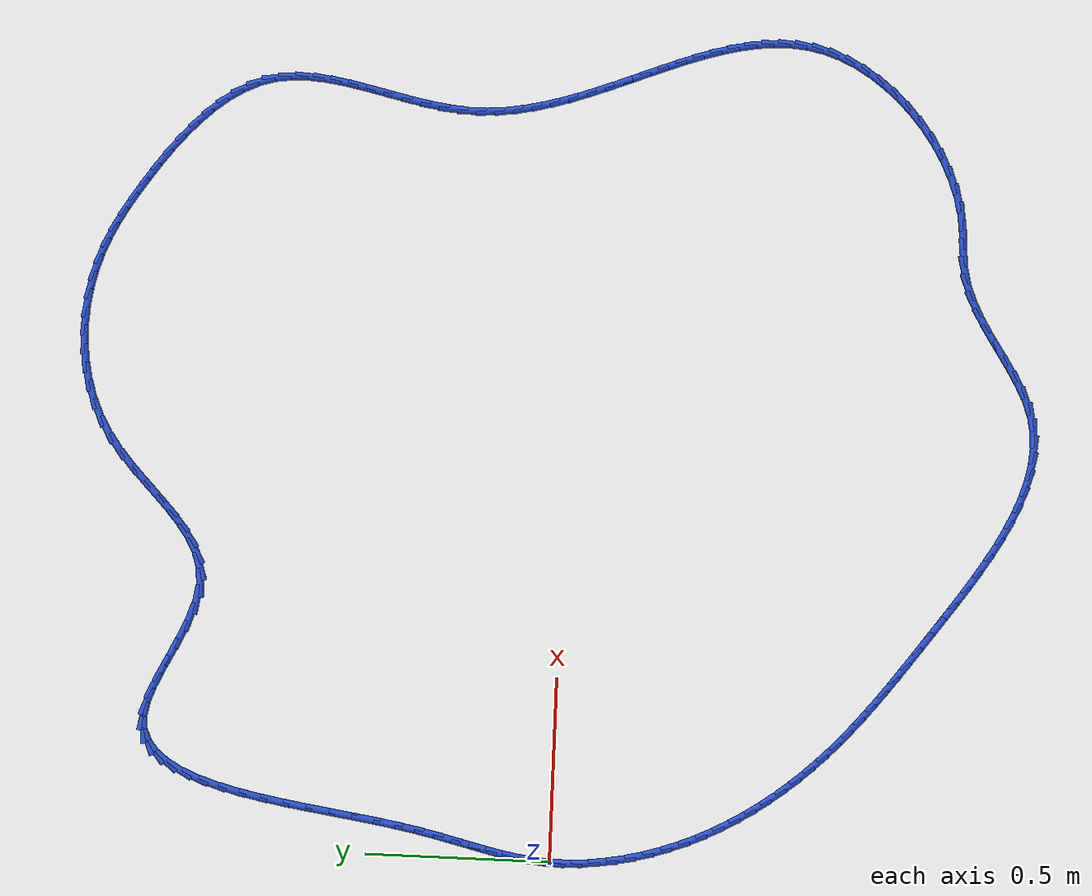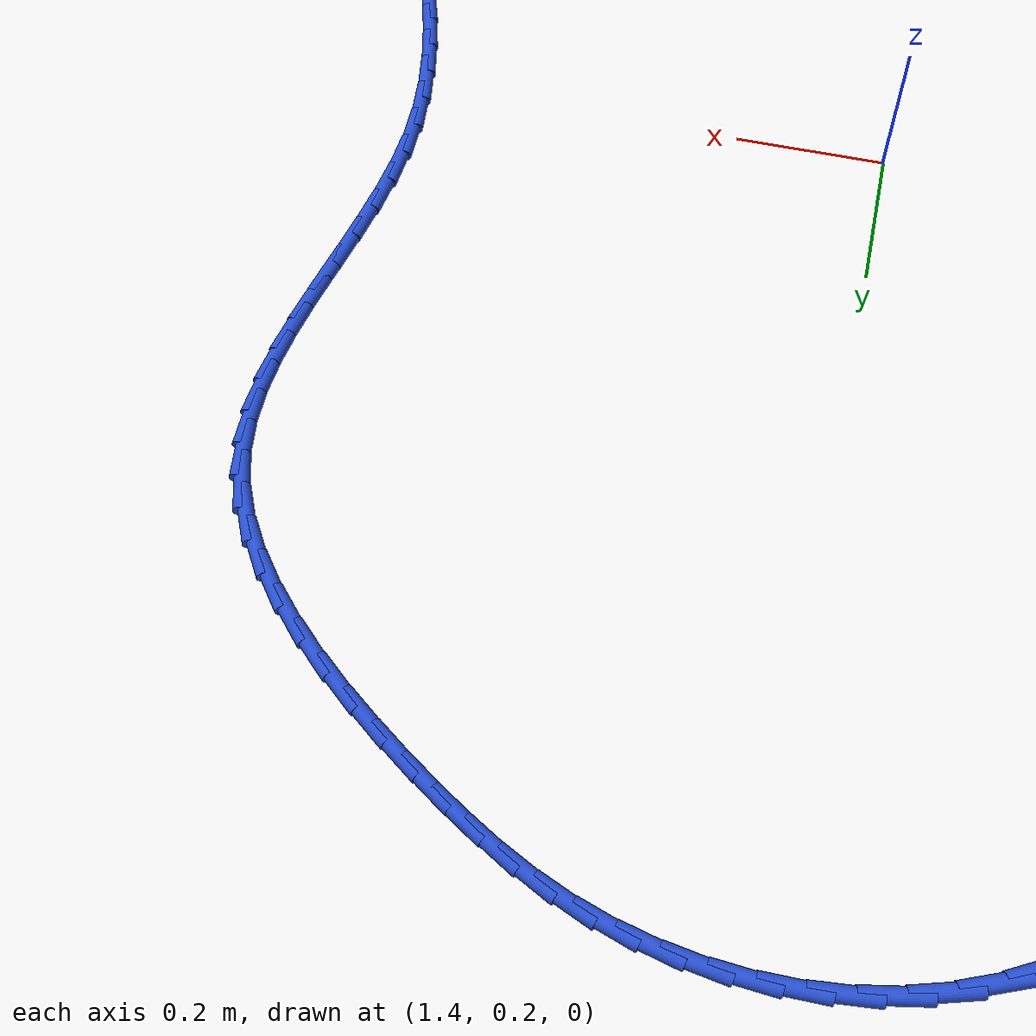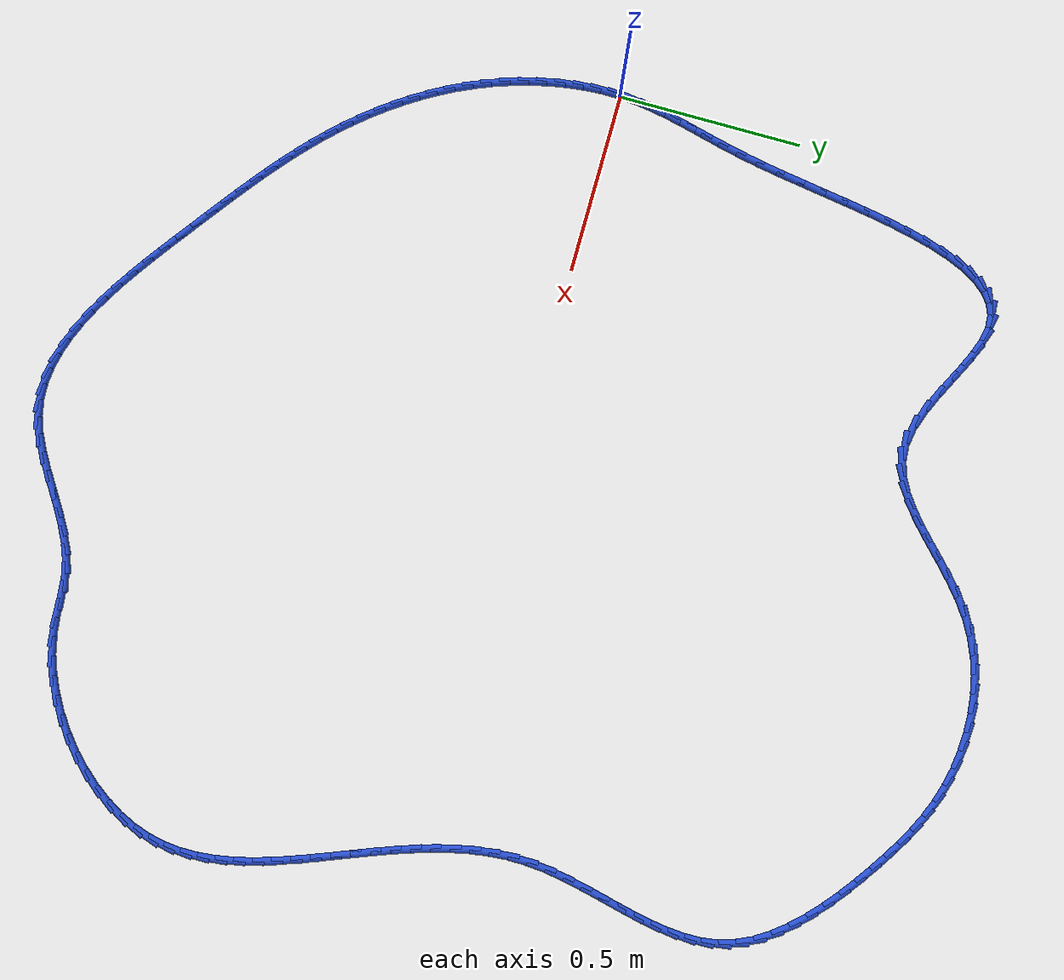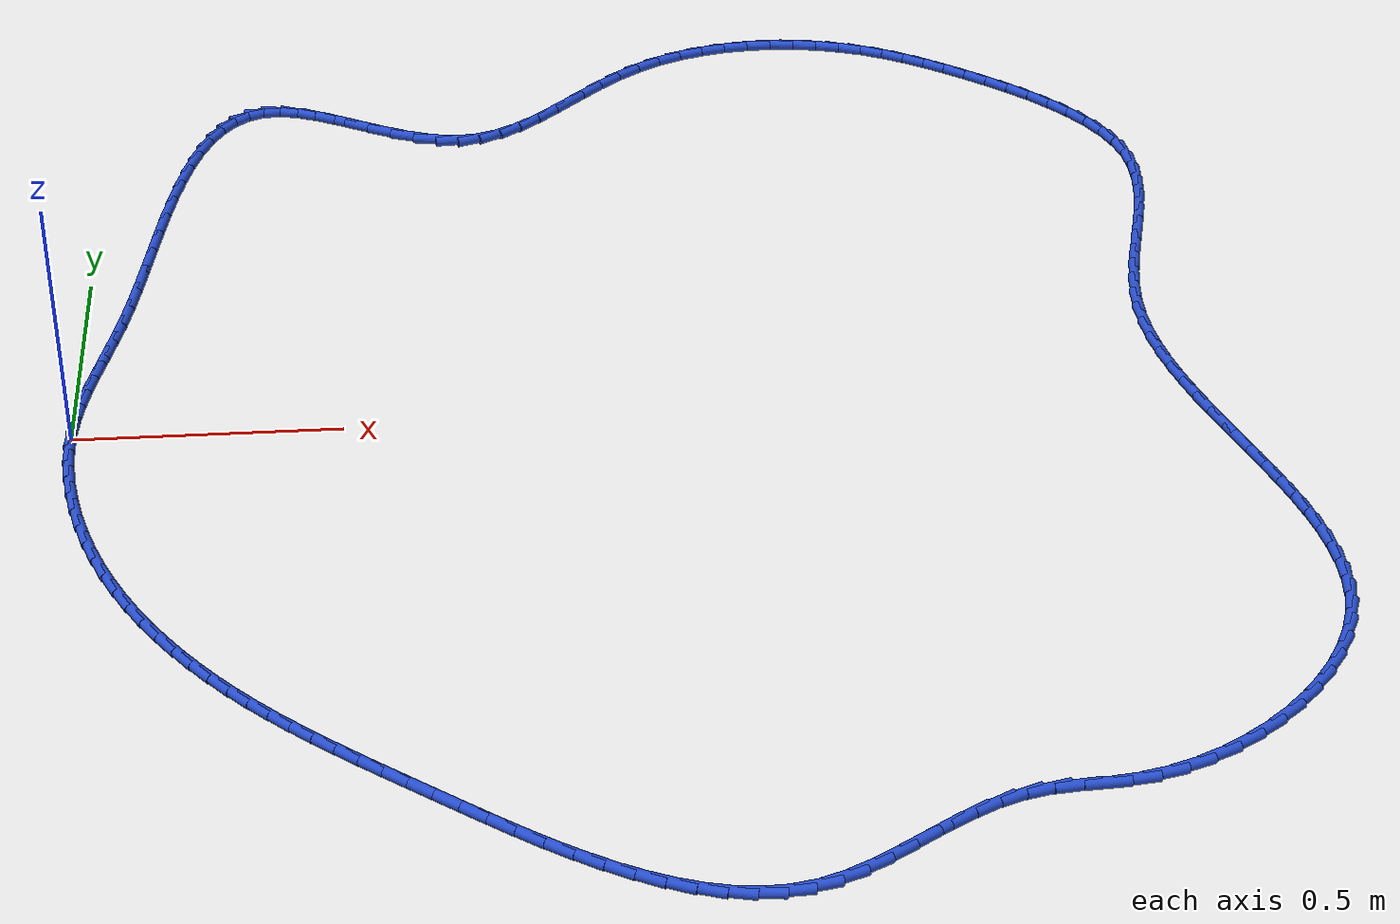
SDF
<sdf version="1.6">
 <world name="default">
  <light name="sun" type="directional">
   <pose>0 0 10 0 -0 0</pose>
   <diffuse>0.8 0.8 0.8 1</diffuse>
   <specular>0.2 0.2 0.2 1</specular>
   <attenuation>
    <range>1000</range>
    <constant>0.9</constant>
    <linear>0.01</linear>
    <quadratic>0.001</quadratic>
   </attenuation>
   <direction>-0.5 0.1 -0.9</direction>
  </light>
  <model name="ground_plane">
   <static>1</static>
   <link name="link">
    <collision name="collision">
     <geometry><plane><normal>0 0 1</normal><size>100 100</size></plane></geometry>
     <surface><friction><ode><mu>100</mu><mu2>50</mu2></ode></friction></surface>
    </collision>
    <visual name="visual">
     <cast_shadows>0</cast_shadows>
     <geometry><plane><normal>0 0 1</normal><size>100 100</size></plane></geometry>
     <material>
      <script><uri>file://media/materials/scripts/gazebo.material</uri><name>Gazebo/WhiteGlow</name></script>
     </material>
    </visual>
   </link>
  </model>
  <gravity>0 0 -9.8</gravity>
  <magnetic_field>6e-06 2.3e-05 -4.2e-05</magnetic_field>
  <atmosphere type="adiabatic"/>
  <physics name="default_physics" default="0" type="ode">
   <max_step_size>0.001</max_step_size>
   <real_time_factor>1</real_time_factor>
   <real_time_update_rate>1000</real_time_update_rate>
  </physics>
  <scene><ambient>0.4 0.4 0.4 1</ambient><background>0.7 0.7 0.7 1</background><shadows>1</shadows></scene>
  <spherical_coordinates>
   <surface_model>EARTH_WGS84</surface_model>
   <latitude_deg>0</latitude_deg>
   <longitude_deg>0</longitude_deg>
   <elevation>0</elevation>
   <heading_deg>0</heading_deg>
  </spherical_coordinates>
  <model name="line">
   <link name="link_0">
    <pose>-6.938893903907228e-18 -1.249000902703301e-16 0.01 0 1.57 1.4895754016602116</pose>
    <collision name="collision">
     <geometry><cylinder><radius>0.01</radius><length>0.08</length></cylinder></geometry>
    </collision>
    <visual name="visual">
     <material>
      <script><name>Gazebo/Blue</name><uri>file://media/materials/scripts/gazebo.material</uri></script>
     </material>
     <geometry><cylinder><radius>0.01</radius><length>0.08</length></cylinder></geometry>
    </visual>
   </link>
   <link name="link_1">
    <pose>0.003737447004198894 0.04591458342012161 0.01 0 1.57 1.428742376575698</pose>
    <collision name="collision">
     <geometry><cylinder><radius>0.01</radius><length>0.08</length></cylinder></geometry>
    </collision>
    <visual name="visual">
     <material>
      <script><name>Gazebo/Blue</name><uri>file://media/materials/scripts/gazebo.material</uri></script>
     </material>
     <geometry><cylinder><radius>0.01</radius><length>0.08</length></cylinder></geometry>
    </visual>
   </link>
   <link name="link_2">
    <pose>0.010216106213988687 0.09121442998399894 0.01 0 1.57 1.3814560206182493</pose>
    <collision name="collision">
     <geometry><cylinder><radius>0.01</radius><length>0.08</length></cylinder></geometry>
    </collision>
    <visual name="visual">
     <material>
      <script><name>Gazebo/Blue</name><uri>file://media/materials/scripts/gazebo.material</uri></script>
     </material>
     <geometry><cylinder><radius>0.01</radius><length>0.08</length></cylinder></geometry>
    </visual>
   </link>
   <link name="link_3">
    <pose>0.018893902228374077 0.1364971727651995 0.01 0 1.57 1.3491577165659407</pose>
    <collision name="collision">
     <geometry><cylinder><radius>0.01</radius><length>0.08</length></cylinder></geometry>
    </collision>
    <visual name="visual">
     <material>
      <script><name>Gazebo/Blue</name><uri>file://media/materials/scripts/gazebo.material</uri></script>
     </material>
     <geometry><cylinder><radius>0.01</radius><length>0.08</length></cylinder></geometry>
    </visual>
   </link>
   <link name="link_4">
    <pose>0.02922875964635978 0.18236044483729097 0.01 0 1.57 1.3320398469157433</pose>
    <collision name="collision">
     <geometry><cylinder><radius>0.01</radius><length>0.08</length></cylinder></geometry>
    </collision>
    <visual name="visual">
     <material>
      <script><name>Gazebo/Blue</name><uri>file://media/materials/scripts/gazebo.material</uri></script>
     </material>
     <geometry><cylinder><radius>0.01</radius><length>0.08</length></cylinder></geometry>
    </visual>
   </link>
   <link name="link_5">
    <pose>0.040678603066950515 0.22940187927384104 0.01 0 1.57 1.329320992105798</pose>
    <collision name="collision">
     <geometry><cylinder><radius>0.01</radius><length>0.08</length></cylinder></geometry>
    </collision>
    <visual name="visual">
     <material>
      <script><name>Gazebo/Blue</name><uri>file://media/materials/scripts/gazebo.material</uri></script>
     </material>
     <geometry><cylinder><radius>0.01</radius><length>0.08</length></cylinder></geometry>
    </visual>
   </link>
   <link name="link_6">
    <pose>0.052701357089150996 0.27821910914841746 0.01 0 1.57 1.3395441022520287</pose>
    <collision name="collision">
     <geometry><cylinder><radius>0.01</radius><length>0.08</length></cylinder></geometry>
    </collision>
    <visual name="visual">
     <material>
      <script><name>Gazebo/Blue</name><uri>file://media/materials/scripts/gazebo.material</uri></script>
     </material>
     <geometry><cylinder><radius>0.01</radius><length>0.08</length></cylinder></geometry>
    </visual>
   </link>
   <link name="link_7">
    <pose>0.06475494631196589 0.32940976753458784 0.01 0 1.57 1.3608283207900278</pose>
    <collision name="collision">
     <geometry><cylinder><radius>0.01</radius><length>0.08</length></cylinder></geometry>
    </collision>
    <visual name="visual">
     <material>
      <script><name>Gazebo/Blue</name><uri>file://media/materials/scripts/gazebo.material</uri></script>
     </material>
     <geometry><cylinder><radius>0.01</radius><length>0.08</length></cylinder></geometry>
    </visual>
   </link>
   <link name="link_8">
    <pose>0.07629729592408209 0.383571486500612 0.01 0 1.57 1.387681911467791</pose>
    <collision name="collision">
     <geometry><cylinder><radius>0.01</radius><length>0.08</length></cylinder></geometry>
    </collision>
    <visual name="visual">
     <material>
      <script><name>Gazebo/Blue</name><uri>file://media/materials/scripts/gazebo.material</uri></script>
     </material>
     <geometry><cylinder><radius>0.01</radius><length>0.08</length></cylinder></geometry>
    </visual>
   </link>
   <link name="link_9">
    <pose>0.08693985716086983 0.44104016229619286 0.01 0 1.57 1.406929505029998</pose>
    <collision name="collision">
     <geometry><cylinder><radius>0.01</radius><length>0.08</length></cylinder></geometry>
    </collision>
    <visual name="visual">
     <material>
      <script><name>Gazebo/Blue</name><uri>file://media/materials/scripts/gazebo.material</uri></script>
     </material>
     <geometry><cylinder><radius>0.01</radius><length>0.08</length></cylinder></geometry>
    </visual>
   </link>
   <link name="link_10">
    <pose>0.09687957149746051 0.5011535298135849 0.01 0 1.57 1.4172507438096182</pose>
    <collision name="collision">
     <geometry><cylinder><radius>0.01</radius><length>0.08</length></cylinder></geometry>
    </collision>
    <visual name="visual">
     <material>
      <script><name>Gazebo/Blue</name><uri>file://media/materials/scripts/gazebo.material</uri></script>
     </material>
     <geometry><cylinder><radius>0.01</radius><length>0.08</length></cylinder></geometry>
    </visual>
   </link>
   <link name="link_11">
    <pose>0.10645292981553517 0.563011415922649 0.01 0 1.57 1.419752158981793</pose>
    <collision name="collision">
     <geometry><cylinder><radius>0.01</radius><length>0.08</length></cylinder></geometry>
    </collision>
    <visual name="visual">
     <material>
      <script><name>Gazebo/Blue</name><uri>file://media/materials/scripts/gazebo.material</uri></script>
     </material>
     <geometry><cylinder><radius>0.01</radius><length>0.08</length></cylinder></geometry>
    </visual>
   </link>
   <link name="link_12">
    <pose>0.11599642299677476 0.6257136474932468 0.01 0 1.57 1.414839581258221</pose>
    <collision name="collision">
     <geometry><cylinder><radius>0.01</radius><length>0.08</length></cylinder></geometry>
    </collision>
    <visual name="visual">
     <material>
      <script><name>Gazebo/Blue</name><uri>file://media/materials/scripts/gazebo.material</uri></script>
     </material>
     <geometry><cylinder><radius>0.01</radius><length>0.08</length></cylinder></geometry>
    </visual>
   </link>
   <link name="link_13">
    <pose>0.12584654192286016 0.6883600513952381 0.01 0 1.57 1.4023137380746789</pose>
    <collision name="collision">
     <geometry><cylinder><radius>0.01</radius><length>0.08</length></cylinder></geometry>
    </collision>
    <visual name="visual">
     <material>
      <script><name>Gazebo/Blue</name><uri>file://media/materials/scripts/gazebo.material</uri></script>
     </material>
     <geometry><cylinder><radius>0.01</radius><length>0.08</length></cylinder></geometry>
    </visual>
   </link>
   <link name="link_14">
    <pose>0.13633977747547235 0.7500504544984846 0.01 0 1.57 1.3813518682268893</pose>
    <collision name="collision">
     <geometry><cylinder><radius>0.01</radius><length>0.08</length></cylinder></geometry>
    </collision>
    <visual name="visual">
     <material>
      <script><name>Gazebo/Blue</name><uri>file://media/materials/scripts/gazebo.material</uri></script>
     </material>
     <geometry><cylinder><radius>0.01</radius><length>0.08</length></cylinder></geometry>
    </visual>
   </link>
   <link name="link_15">
    <pose>0.14781262053629224 0.8098846836728472 0.01 0 1.57 1.3503755823690906</pose>
    <collision name="collision">
     <geometry><cylinder><radius>0.01</radius><length>0.08</length></cylinder></geometry>
    </collision>
    <visual name="visual">
     <material>
      <script><name>Gazebo/Blue</name><uri>file://media/materials/scripts/gazebo.material</uri></script>
     </material>
     <geometry><cylinder><radius>0.01</radius><length>0.08</length></cylinder></geometry>
    </visual>
   </link>
   <link name="link_16">
    <pose>0.16060156198700087 0.8669625657881869 0.01 0 1.57 1.3067746035784935</pose>
    <collision name="collision">
     <geometry><cylinder><radius>0.01</radius><length>0.08</length></cylinder></geometry>
    </collision>
    <visual name="visual">
     <material>
      <script><name>Gazebo/Blue</name><uri>file://media/materials/scripts/gazebo.material</uri></script>
     </material>
     <geometry><cylinder><radius>0.01</radius><length>0.08</length></cylinder></geometry>
    </visual>
   </link>
   <link name="link_17">
    <pose>0.1750430927092791 0.9203839277143643 0.01 0 1.57 1.2464255359530974</pose>
    <collision name="collision">
     <geometry><cylinder><radius>0.01</radius><length>0.08</length></cylinder></geometry>
    </collision>
    <visual name="visual">
     <material>
      <script><name>Gazebo/Blue</name><uri>file://media/materials/scripts/gazebo.material</uri></script>
     </material>
     <geometry><cylinder><radius>0.01</radius><length>0.08</length></cylinder></geometry>
    </visual>
   </link>
   <link name="link_18">
    <pose>0.19147370358480784 0.9692485963212404 0.01 0 1.57 1.1629337131102255</pose>
    <collision name="collision">
     <geometry><cylinder><radius>0.01</radius><length>0.08</length></cylinder></geometry>
    </collision>
    <visual name="visual">
     <material>
      <script><name>Gazebo/Blue</name><uri>file://media/materials/scripts/gazebo.material</uri></script>
     </material>
     <geometry><cylinder><radius>0.01</radius><length>0.08</length></cylinder></geometry>
    </visual>
   </link>
   <link name="link_19">
    <pose>0.21022988549526805 1.012656398478676 0.01 0 1.57 1.0466516601180527</pose>
    <collision name="collision">
     <geometry><cylinder><radius>0.01</radius><length>0.08</length></cylinder></geometry>
    </collision>
    <visual name="visual">
     <material>
      <script><name>Gazebo/Blue</name><uri>file://media/materials/scripts/gazebo.material</uri></script>
     </material>
     <geometry><cylinder><radius>0.01</radius><length>0.08</length></cylinder></geometry>
    </visual>
   </link>
   <link name="link_20">
    <pose>0.23164812932234075 1.0497071610565327 0.01 0 1.57 0.8842579940270712</pose>
    <collision name="collision">
     <geometry><cylinder><radius>0.01</radius><length>0.08</length></cylinder></geometry>
    </collision>
    <visual name="visual">
     <material>
      <script><name>Gazebo/Blue</name><uri>file://media/materials/scripts/gazebo.material</uri></script>
     </material>
     <geometry><cylinder><radius>0.01</radius><length>0.08</length></cylinder></geometry>
    </visual>
   </link>
   <link name="link_21">
    <pose>0.25606492594770686 1.0795007109246708 0.01 0 1.57 0.6621961379086412</pose>
    <collision name="collision">
     <geometry><cylinder><radius>0.01</radius><length>0.08</length></cylinder></geometry>
    </collision>
    <visual name="visual">
     <material>
      <script><name>Gazebo/Blue</name><uri>file://media/materials/scripts/gazebo.material</uri></script>
     </material>
     <geometry><cylinder><radius>0.01</radius><length>0.08</length></cylinder></geometry>
    </visual>
   </link>
   <link name="link_22">
    <pose>0.2838167662530473 1.1011368749529515 0.01 0 1.57 0.38076025608026276</pose>
    <collision name="collision">
     <geometry><cylinder><radius>0.01</radius><length>0.08</length></cylinder></geometry>
    </collision>
    <visual name="visual">
     <material>
      <script><name>Gazebo/Blue</name><uri>file://media/materials/scripts/gazebo.material</uri></script>
     </material>
     <geometry><cylinder><radius>0.01</radius><length>0.08</length></cylinder></geometry>
    </visual>
   </link>
   <link name="link_23">
    <pose>0.31524014112004295 1.1137154800112357 0.01 0 1.57 0.0738358753459542</pose>
    <collision name="collision">
     <geometry><cylinder><radius>0.01</radius><length>0.08</length></cylinder></geometry>
    </collision>
    <visual name="visual">
     <material>
      <script><name>Gazebo/Blue</name><uri>file://media/materials/scripts/gazebo.material</uri></script>
     </material>
     <geometry><cylinder><radius>0.01</radius><length>0.08</length></cylinder></geometry>
    </visual>
   </link>
   <link name="link_24">
    <pose>0.35067154143037493 1.1163363529693844 0.01 0 1.57 -0.19113792418683165</pose>
    <collision name="collision">
     <geometry><cylinder><radius>0.01</radius><length>0.08</length></cylinder></geometry>
    </collision>
    <visual name="visual">
     <material>
      <script><name>Gazebo/Blue</name><uri>file://media/materials/scripts/gazebo.material</uri></script>
     </material>
     <geometry><cylinder><radius>0.01</radius><length>0.08</length></cylinder></geometry>
    </visual>
   </link>
   <link name="link_25">
    <pose>0.39025907240353497 1.1086761614166027 0.01 0 1.57 -0.3521386740614026</pose>
    <collision name="collision">
     <geometry><cylinder><radius>0.01</radius><length>0.08</length></cylinder></geometry>
    </collision>
    <visual name="visual">
     <material>
      <script><name>Gazebo/Blue</name><uri>file://media/materials/scripts/gazebo.material</uri></script>
     </material>
     <geometry><cylinder><radius>0.01</radius><length>0.08</length></cylinder></geometry>
    </visual>
   </link>
   <link name="link_26">
    <pose>0.4333579912013606 1.092839289778902 0.01 0 1.57 -0.435142360565901</pose>
    <collision name="collision">
     <geometry><cylinder><radius>0.01</radius><length>0.08</length></cylinder></geometry>
    </collision>
    <visual name="visual">
     <material>
      <script><name>Gazebo/Blue</name><uri>file://media/materials/scripts/gazebo.material</uri></script>
     </material>
     <geometry><cylinder><radius>0.01</radius><length>0.08</length></cylinder></geometry>
    </visual>
   </link>
   <link name="link_27">
    <pose>0.47911500943818575 1.0715686931794475 0.01 0 1.57 -0.4666781961913654</pose>
    <collision name="collision">
     <geometry><cylinder><radius>0.01</radius><length>0.08</length></cylinder></geometry>
    </collision>
    <visual name="visual">
     <material>
      <script><name>Gazebo/Blue</name><uri>file://media/materials/scripts/gazebo.material</uri></script>
     </material>
     <geometry><cylinder><radius>0.01</radius><length>0.08</length></cylinder></geometry>
    </visual>
   </link>
   <link name="link_28">
    <pose>0.5266768377633952 1.0476073296960968 0.01 0 1.57 -0.45790078772490445</pose>
    <collision name="collision">
     <geometry><cylinder><radius>0.01</radius><length>0.08</length></cylinder></geometry>
    </collision>
    <visual name="visual">
     <material>
      <script><name>Gazebo/Blue</name><uri>file://media/materials/scripts/gazebo.material</uri></script>
     </material>
     <geometry><cylinder><radius>0.01</radius><length>0.08</length></cylinder></geometry>
    </visual>
   </link>
   <link name="link_29">
    <pose>0.5751901868263752 1.0236981574067077 0.01 0 1.57 -0.4097562356419065</pose>
    <collision name="collision">
     <geometry><cylinder><radius>0.01</radius><length>0.08</length></cylinder></geometry>
    </collision>
    <visual name="visual">
     <material>
      <script><name>Gazebo/Blue</name><uri>file://media/materials/scripts/gazebo.material</uri></script>
     </material>
     <geometry><cylinder><radius>0.01</radius><length>0.08</length></cylinder></geometry>
    </visual>
   </link>
   <link name="link_30">
    <pose>0.6238017672765099 1.0025841343891377 0.01 0 1.57 -0.3146579462180876</pose>
    <collision name="collision">
     <geometry><cylinder><radius>0.01</radius><length>0.08</length></cylinder></geometry>
    </collision>
    <visual name="visual">
     <material>
      <script><name>Gazebo/Blue</name><uri>file://media/materials/scripts/gazebo.material</uri></script>
     </material>
     <geometry><cylinder><radius>0.01</radius><length>0.08</length></cylinder></geometry>
    </visual>
   </link>
   <link name="link_31">
    <pose>0.6716582897631851 0.9870082187212441 0.01 0 1.57 -0.15644379240625356</pose>
    <collision name="collision">
     <geometry><cylinder><radius>0.01</radius><length>0.08</length></cylinder></geometry>
    </collision>
    <visual name="visual">
     <material>
      <script><name>Gazebo/Blue</name><uri>file://media/materials/scripts/gazebo.material</uri></script>
     </material>
     <geometry><cylinder><radius>0.01</radius><length>0.08</length></cylinder></geometry>
    </visual>
   </link>
   <link name="link_32">
    <pose>0.7179064649357865 0.9797133684808854 0.01 0 1.57 0.07506693497170534</pose>
    <collision name="collision">
     <geometry><cylinder><radius>0.01</radius><length>0.08</length></cylinder></geometry>
    </collision>
    <visual name="visual">
     <material>
      <script><name>Gazebo/Blue</name><uri>file://media/materials/scripts/gazebo.material</uri></script>
     </material>
     <geometry><cylinder><radius>0.01</radius><length>0.08</length></cylinder></geometry>
    </visual>
   </link>
   <link name="link_33">
    <pose>0.7618236026025955 0.9830162997853993 0.01 0 1.57 0.3090289596613219</pose>
    <collision name="collision">
     <geometry><cylinder><radius>0.01</radius><length>0.08</length></cylinder></geometry>
    </collision>
    <visual name="visual">
     <material>
      <script><name>Gazebo/Blue</name><uri>file://media/materials/scripts/gazebo.material</uri></script>
     </material>
     <geometry><cylinder><radius>0.01</radius><length>0.08</length></cylinder></geometry>
    </visual>
   </link>
   <link name="link_34">
    <pose>0.8035721628725282 0.996344826536485 0.01 0 1.57 0.4936535747990462</pose>
    <collision name="collision">
     <geometry><cylinder><radius>0.01</radius><length>0.08</length></cylinder></geometry>
    </collision>
    <visual name="visual">
     <material>
      <script><name>Gazebo/Blue</name><uri>file://media/materials/scripts/gazebo.material</uri></script>
     </material>
     <geometry><cylinder><radius>0.01</radius><length>0.08</length></cylinder></geometry>
    </visual>
   </link>
   <link name="link_35">
    <pose>0.8436820367591463 1.0179275629589475 0.01 0 1.57 0.6236859543090459</pose>
    <collision name="collision">
     <geometry><cylinder><radius>0.01</radius><length>0.08</length></cylinder></geometry>
    </collision>
    <visual name="visual">
     <material>
      <script><name>Gazebo/Blue</name><uri>file://media/materials/scripts/gazebo.material</uri></script>
     </material>
     <geometry><cylinder><radius>0.01</radius><length>0.08</length></cylinder></geometry>
    </visual>
   </link>
   <link name="link_36">
    <pose>0.8826843056840552 1.0459892380928566 0.01 0 1.57 0.7060550935219422</pose>
    <collision name="collision">
     <geometry><cylinder><radius>0.01</radius><length>0.08</length></cylinder></geometry>
    </collision>
    <visual name="visual">
     <material>
      <script><name>Gazebo/Blue</name><uri>file://media/materials/scripts/gazebo.material</uri></script>
     </material>
     <geometry><cylinder><radius>0.01</radius><length>0.08</length></cylinder></geometry>
    </visual>
   </link>
   <link name="link_37">
    <pose>0.9211100510688603 1.0787545809782826 0.01 0 1.57 0.7491454299006022</pose>
    <collision name="collision">
     <geometry><cylinder><radius>0.01</radius><length>0.08</length></cylinder></geometry>
    </collision>
    <visual name="visual">
     <material>
      <script><name>Gazebo/Blue</name><uri>file://media/materials/scripts/gazebo.material</uri></script>
     </material>
     <geometry><cylinder><radius>0.01</radius><length>0.08</length></cylinder></geometry>
    </visual>
   </link>
   <link name="link_38">
    <pose>0.9594903543351674 1.1144483206552955 0.01 0 1.57 0.7587369063733563</pose>
    <collision name="collision">
     <geometry><cylinder><radius>0.01</radius><length>0.08</length></cylinder></geometry>
    </collision>
    <visual name="visual">
     <material>
      <script><name>Gazebo/Blue</name><uri>file://media/materials/scripts/gazebo.material</uri></script>
     </material>
     <geometry><cylinder><radius>0.01</radius><length>0.08</length></cylinder></geometry>
    </visual>
   </link>
   <link name="link_39">
    <pose>0.9983562969045815 1.1512951861639658 0.01 0 1.57 0.7373722036935721</pose>
    <collision name="collision">
     <geometry><cylinder><radius>0.01</radius><length>0.08</length></cylinder></geometry>
    </collision>
    <visual name="visual">
     <material>
      <script><name>Gazebo/Blue</name><uri>file://media/materials/scripts/gazebo.material</uri></script>
     </material>
     <geometry><cylinder><radius>0.01</radius><length>0.08</length></cylinder></geometry>
    </visual>
   </link>
   <link name="link_40">
    <pose>1.0382389601987079 1.1875199065443631 0.01 0 1.57 0.684711540677317</pose>
    <collision name="collision">
     <geometry><cylinder><radius>0.01</radius><length>0.08</length></cylinder></geometry>
    </collision>
    <visual name="visual">
     <material>
      <script><name>Gazebo/Blue</name><uri>file://media/materials/scripts/gazebo.material</uri></script>
     </material>
     <geometry><cylinder><radius>0.01</radius><length>0.08</length></cylinder></geometry>
    </visual>
   </link>
   <link name="link_41">
    <pose>1.079669425639153 1.2213472108365582 0.01 0 1.57 0.5984856214067509</pose>
    <collision name="collision">
     <geometry><cylinder><radius>0.01</radius><length>0.08</length></cylinder></geometry>
    </collision>
    <visual name="visual">
     <material>
      <script><name>Gazebo/Blue</name><uri>file://media/materials/scripts/gazebo.material</uri></script>
     </material>
     <geometry><cylinder><radius>0.01</radius><length>0.08</length></cylinder></geometry>
    </visual>
   </link>
   <link name="link_42">
    <pose>1.1231731549273072 1.2510130970443436 0.01 0 1.57 0.4909132639672876</pose>
    <collision name="collision">
     <geometry><cylinder><radius>0.01</radius><length>0.08</length></cylinder></geometry>
    </collision>
    <visual name="visual">
     <material>
      <script><name>Gazebo/Blue</name><uri>file://media/materials/scripts/gazebo.material</uri></script>
     </material>
     <geometry><cylinder><radius>0.01</radius><length>0.08</length></cylinder></geometry>
    </visual>
   </link>
   <link name="link_43">
    <pose>1.168919621076455 1.2754674107403128 0.01 0 1.57 0.385621193769937</pose>
    <collision name="collision">
     <geometry><cylinder><radius>0.01</radius><length>0.08</length></cylinder></geometry>
    </collision>
    <visual name="visual">
     <material>
      <script><name>Gazebo/Blue</name><uri>file://media/materials/scripts/gazebo.material</uri></script>
     </material>
     <geometry><cylinder><radius>0.01</radius><length>0.08</length></cylinder></geometry>
    </visual>
   </link>
   <link name="link_44">
    <pose>1.2165154209391176 1.2947887068980033 0.01 0 1.57 0.2851914351242984</pose>
    <collision name="collision">
     <geometry><cylinder><radius>0.01</radius><length>0.08</length></cylinder></geometry>
    </collision>
    <visual name="visual">
     <material>
      <script><name>Gazebo/Blue</name><uri>file://media/materials/scripts/gazebo.material</uri></script>
     </material>
     <geometry><cylinder><radius>0.01</radius><length>0.08</length></cylinder></geometry>
    </visual>
   </link>
   <link name="link_45">
    <pose>1.2655174116936636 1.309155281147472 0.01 0 1.57 0.18963095166697283</pose>
    <collision name="collision">
     <geometry><cylinder><radius>0.01</radius><length>0.08</length></cylinder></geometry>
    </collision>
    <visual name="visual">
     <material>
      <script><name>Gazebo/Blue</name><uri>file://media/materials/scripts/gazebo.material</uri></script>
     </material>
     <geometry><cylinder><radius>0.01</radius><length>0.08</length></cylinder></geometry>
    </visual>
   </link>
   <link name="link_46">
    <pose>1.315482450518464 1.318745429118775 0.01 0 1.57 0.09856091477869121</pose>
    <collision name="collision">
     <geometry><cylinder><radius>0.01</radius><length>0.08</length></cylinder></geometry>
    </collision>
    <visual name="visual">
     <material>
      <script><name>Gazebo/Blue</name><uri>file://media/materials/scripts/gazebo.material</uri></script>
     </material>
     <geometry><cylinder><radius>0.01</radius><length>0.08</length></cylinder></geometry>
    </visual>
   </link>
   <link name="link_47">
    <pose>1.3659673945918875 1.3237374464419696 0.01 0 1.57 0.011316031862768706</pose>
    <collision name="collision">
     <geometry><cylinder><radius>0.01</radius><length>0.08</length></cylinder></geometry>
    </collision>
    <visual name="visual">
     <material>
      <script><name>Gazebo/Blue</name><uri>file://media/materials/scripts/gazebo.material</uri></script>
     </material>
     <geometry><cylinder><radius>0.01</radius><length>0.08</length></cylinder></geometry>
    </visual>
   </link>
   <link name="link_48">
    <pose>1.4165291010923058 1.3243096287471123 0.01 0 1.57 -0.07297177033497682</pose>
    <collision name="collision">
     <geometry><cylinder><radius>0.01</radius><length>0.08</length></cylinder></geometry>
    </collision>
    <visual name="visual">
     <material>
      <script><name>Gazebo/Blue</name><uri>file://media/materials/scripts/gazebo.material</uri></script>
     </material>
     <geometry><cylinder><radius>0.01</radius><length>0.08</length></cylinder></geometry>
    </visual>
   </link>
   <link name="link_49">
    <pose>1.4667244271980877 1.3206402716642602 0.01 0 1.57 -0.15531435136081623</pose>
    <collision name="collision">
     <geometry><cylinder><radius>0.01</radius><length>0.08</length></cylinder></geometry>
    </collision>
    <visual name="visual">
     <material>
      <script><name>Gazebo/Blue</name><uri>file://media/materials/scripts/gazebo.material</uri></script>
     </material>
     <geometry><cylinder><radius>0.01</radius><length>0.08</length></cylinder></geometry>
    </visual>
   </link>
   <link name="link_50">
    <pose>1.5161102300876028 1.3129076708234693 0.01 0 1.57 -0.2368331651425001</pose>
    <collision name="collision">
     <geometry><cylinder><radius>0.01</radius><length>0.08</length></cylinder></geometry>
    </collision>
    <visual name="visual">
     <material>
      <script><name>Gazebo/Blue</name><uri>file://media/materials/scripts/gazebo.material</uri></script>
     </material>
     <geometry><cylinder><radius>0.01</radius><length>0.08</length></cylinder></geometry>
    </visual>
   </link>
   <link name="link_51">
    <pose>1.564243366939222 1.3012901218547963 0.01 0 1.57 -0.3187390594051004</pose>
    <collision name="collision">
     <geometry><cylinder><radius>0.01</radius><length>0.08</length></cylinder></geometry>
    </collision>
    <visual name="visual">
     <material>
      <script><name>Gazebo/Blue</name><uri>file://media/materials/scripts/gazebo.material</uri></script>
     </material>
     <geometry><cylinder><radius>0.01</radius><length>0.08</length></cylinder></geometry>
    </visual>
   </link>
   <link name="link_52">
    <pose>1.6106812710571592 1.2859660512543754 0.01 0 1.57 -0.3991932722505689</pose>
    <collision name="collision">
     <geometry><cylinder><radius>0.01</radius><length>0.08</length></cylinder></geometry>
    </collision>
    <visual name="visual">
     <material>
      <script><name>Gazebo/Blue</name><uri>file://media/materials/scripts/gazebo.material</uri></script>
     </material>
     <geometry><cylinder><radius>0.01</radius><length>0.08</length></cylinder></geometry>
    </visual>
   </link>
   <link name="link_53">
    <pose>1.6552348368600316 1.26717145881058 0.01 0 1.57 -0.4694994752697667</pose>
    <collision name="collision">
     <geometry><cylinder><radius>0.01</radius><length>0.08</length></cylinder></geometry>
    </collision>
    <visual name="visual">
     <material>
      <script><name>Gazebo/Blue</name><uri>file://media/materials/scripts/gazebo.material</uri></script>
     </material>
     <geometry><cylinder><radius>0.01</radius><length>0.08</length></cylinder></geometry>
    </visual>
   </link>
   <link name="link_54">
    <pose>1.6983649424370144 1.2452899870770489 0.01 0 1.57 -0.5263733945198128</pose>
    <collision name="collision">
     <geometry><cylinder><radius>0.01</radius><length>0.08</length></cylinder></geometry>
    </collision>
    <visual name="visual">
     <material>
      <script><name>Gazebo/Blue</name><uri>file://media/materials/scripts/gazebo.material</uri></script>
     </material>
     <geometry><cylinder><radius>0.01</radius><length>0.08</length></cylinder></geometry>
    </visual>
   </link>
   <link name="link_55">
    <pose>1.7406351977806955 1.220728613997195 0.01 0 1.57 -0.568821658029842</pose>
    <collision name="collision">
     <geometry><cylinder><radius>0.01</radius><length>0.08</length></cylinder></geometry>
    </collision>
    <visual name="visual">
     <material>
      <script><name>Gazebo/Blue</name><uri>file://media/materials/scripts/gazebo.material</uri></script>
     </material>
     <geometry><cylinder><radius>0.01</radius><length>0.08</length></cylinder></geometry>
    </visual>
   </link>
   <link name="link_56">
    <pose>1.7826092128836646 1.1938943175144325 0.01 0 1.57 -0.5977009438417707</pose>
    <collision name="collision">
     <geometry><cylinder><radius>0.01</radius><length>0.08</length></cylinder></geometry>
    </collision>
    <visual name="visual">
     <material>
      <script><name>Gazebo/Blue</name><uri>file://media/materials/scripts/gazebo.material</uri></script>
     </material>
     <geometry><cylinder><radius>0.01</radius><length>0.08</length></cylinder></geometry>
    </visual>
   </link>
   <link name="link_57">
    <pose>1.824791903198454 1.1651777344412386 0.01 0 1.57 -0.6254450036527809</pose>
    <collision name="collision">
     <geometry><cylinder><radius>0.01</radius><length>0.08</length></cylinder></geometry>
    </collision>
    <visual name="visual">
     <material>
      <script><name>Gazebo/Blue</name><uri>file://media/materials/scripts/gazebo.material</uri></script>
     </material>
     <geometry><cylinder><radius>0.01</radius><length>0.08</length></cylinder></geometry>
    </visual>
   </link>
   <link name="link_58">
    <pose>1.866918822145615 1.1347553037159677 0.01 0 1.57 -0.6611488873387801</pose>
    <collision name="collision">
     <geometry><cylinder><radius>0.01</radius><length>0.08</length></cylinder></geometry>
    </collision>
    <visual name="visual">
     <material>
      <script><name>Gazebo/Blue</name><uri>file://media/materials/scripts/gazebo.material</uri></script>
     </material>
     <geometry><cylinder><radius>0.01</radius><length>0.08</length></cylinder></geometry>
    </visual>
   </link>
   <link name="link_59">
    <pose>1.9081844395417216 1.102652821337921 0.01 0 1.57 -0.7061119390348113</pose>
    <collision name="collision">
     <geometry><cylinder><radius>0.01</radius><length>0.08</length></cylinder></geometry>
    </collision>
    <visual name="visual">
     <material>
      <script><name>Gazebo/Blue</name><uri>file://media/materials/scripts/gazebo.material</uri></script>
     </material>
     <geometry><cylinder><radius>0.01</radius><length>0.08</length></cylinder></geometry>
    </visual>
   </link>
   <link name="link_60">
    <pose>1.9477719669703852 1.0688929489048205 0.01 0 1.57 -0.7619769733917123</pose>
    <collision name="collision">
     <geometry><cylinder><radius>0.01</radius><length>0.08</length></cylinder></geometry>
    </collision>
    <visual name="visual">
     <material>
      <script><name>Gazebo/Blue</name><uri>file://media/materials/scripts/gazebo.material</uri></script>
     </material>
     <geometry><cylinder><radius>0.01</radius><length>0.08</length></cylinder></geometry>
    </visual>
   </link>
   <link name="link_61">
    <pose>1.9848646160152164 1.0334983480143887 0.01 0 1.57 -0.83093514034293</pose>
    <collision name="collision">
     <geometry><cylinder><radius>0.01</radius><length>0.08</length></cylinder></geometry>
    </collision>
    <visual name="visual">
     <material>
      <script><name>Gazebo/Blue</name><uri>file://media/materials/scripts/gazebo.material</uri></script>
     </material>
     <geometry><cylinder><radius>0.01</radius><length>0.08</length></cylinder></geometry>
    </visual>
   </link>
   <link name="link_62">
    <pose>2.018645598259826 0.9964916802643485 0.01 0 1.57 -0.9156993403272001</pose>
    <collision name="collision">
     <geometry><cylinder><radius>0.01</radius><length>0.08</length></cylinder></geometry>
    </collision>
    <visual name="visual">
     <material>
      <script><name>Gazebo/Blue</name><uri>file://media/materials/scripts/gazebo.material</uri></script>
     </material>
     <geometry><cylinder><radius>0.01</radius><length>0.08</length></cylinder></geometry>
    </visual>
   </link>
   <link name="link_63">
    <pose>2.0482981252878254 0.9578956072524222 0.01 0 1.57 -1.0192911817715398</pose>
    <collision name="collision">
     <geometry><cylinder><radius>0.01</radius><length>0.08</length></cylinder></geometry>
    </collision>
    <visual name="visual">
     <material>
      <script><name>Gazebo/Blue</name><uri>file://media/materials/scripts/gazebo.material</uri></script>
     </material>
     <geometry><cylinder><radius>0.01</radius><length>0.08</length></cylinder></geometry>
    </visual>
   </link>
   <link name="link_64">
    <pose>2.073005408682825 0.9177327905763331 0.01 0 1.57 -1.1444158587426554</pose>
    <collision name="collision">
     <geometry><cylinder><radius>0.01</radius><length>0.08</length></cylinder></geometry>
    </collision>
    <visual name="visual">
     <material>
      <script><name>Gazebo/Blue</name><uri>file://media/materials/scripts/gazebo.material</uri></script>
     </material>
     <geometry><cylinder><radius>0.01</radius><length>0.08</length></cylinder></geometry>
    </visual>
   </link>
   <link name="link_65">
    <pose>2.091950660028435 0.8760258918338028 0.01 0 1.57 -1.2910443522502602</pose>
    <collision name="collision">
     <geometry><cylinder><radius>0.01</radius><length>0.08</length></cylinder></geometry>
    </collision>
    <visual name="visual">
     <material>
      <script><name>Gazebo/Blue</name><uri>file://media/materials/scripts/gazebo.material</uri></script>
     </material>
     <geometry><cylinder><radius>0.01</radius><length>0.08</length></cylinder></geometry>
    </visual>
   </link>
   <link name="link_66">
    <pose>2.1043685030918136 0.8328011915691826 0.01 0 1.57 -1.436143403753044</pose>
    <collision name="collision">
     <geometry><cylinder><radius>0.01</radius><length>0.08</length></cylinder></geometry>
    </collision>
    <visual name="visual">
     <material>
      <script><name>Gazebo/Blue</name><uri>file://media/materials/scripts/gazebo.material</uri></script>
     </material>
     <geometry><cylinder><radius>0.01</radius><length>0.08</length></cylinder></geometry>
    </visual>
   </link>
   <link name="link_67">
    <pose>2.1104175187452676 0.7881500084407481 0.01 0 1.57 -1.556895570159781</pose>
    <collision name="collision">
     <geometry><cylinder><radius>0.01</radius><length>0.08</length></cylinder></geometry>
    </collision>
    <visual name="visual">
     <material>
      <script><name>Gazebo/Blue</name><uri>file://media/materials/scripts/gazebo.material</uri></script>
     </material>
     <geometry><cylinder><radius>0.01</radius><length>0.08</length></cylinder></geometry>
    </visual>
   </link>
   <link name="link_68">
    <pose>2.111056022365932 0.7422199550878941 0.01 0 1.57 1.4904906124761526</pose>
    <collision name="collision">
     <geometry><cylinder><radius>0.01</radius><length>0.08</length></cylinder></geometry>
    </collision>
    <visual name="visual">
     <material>
      <script><name>Gazebo/Blue</name><uri>file://media/materials/scripts/gazebo.material</uri></script>
     </material>
     <geometry><cylinder><radius>0.01</radius><length>0.08</length></cylinder></geometry>
    </visual>
   </link>
   <link name="link_69">
    <pose>2.1072687345185246 0.6951605028332717 0.01 0 1.57 1.4214493329029483</pose>
    <collision name="collision">
     <geometry><cylinder><radius>0.01</radius><length>0.08</length></cylinder></geometry>
    </collision>
    <visual name="visual">
     <material>
      <script><name>Gazebo/Blue</name><uri>file://media/materials/scripts/gazebo.material</uri></script>
     </material>
     <geometry><cylinder><radius>0.01</radius><length>0.08</length></cylinder></geometry>
    </visual>
   </link>
   <link name="link_70">
    <pose>2.1000403757677613 0.6471211229995287 0.01 0 1.57 1.3751575805137368</pose>
    <collision name="collision">
     <geometry><cylinder><radius>0.01</radius><length>0.08</length></cylinder></geometry>
    </collision>
    <visual name="visual">
     <material>
      <script><name>Gazebo/Blue</name><uri>file://media/materials/scripts/gazebo.material</uri></script>
     </material>
     <geometry><cylinder><radius>0.01</radius><length>0.08</length></cylinder></geometry>
    </visual>
   </link>
   <link name="link_71">
    <pose>2.090355666678359 0.5982512869093144 0.01 0 1.57 1.3493396641045625</pose>
    <collision name="collision">
     <geometry><cylinder><radius>0.01</radius><length>0.08</length></cylinder></geometry>
    </collision>
    <visual name="visual">
     <material>
      <script><name>Gazebo/Blue</name><uri>file://media/materials/scripts/gazebo.material</uri></script>
     </material>
     <geometry><cylinder><radius>0.01</radius><length>0.08</length></cylinder></geometry>
    </visual>
   </link>
   <link name="link_72">
    <pose>2.0791993278150365 0.5487004658852792 0.01 0 1.57 1.3423717937538475</pose>
    <collision name="collision">
     <geometry><cylinder><radius>0.01</radius><length>0.08</length></cylinder></geometry>
    </collision>
    <visual name="visual">
     <material>
      <script><name>Gazebo/Blue</name><uri>file://media/materials/scripts/gazebo.material</uri></script>
     </material>
     <geometry><cylinder><radius>0.01</radius><length>0.08</length></cylinder></geometry>
    </visual>
   </link>
   <link name="link_73">
    <pose>2.0675560797425088 0.4986181312500711 0.01 0 1.57 1.3534282449816455</pose>
    <collision name="collision">
     <geometry><cylinder><radius>0.01</radius><length>0.08</length></cylinder></geometry>
    </collision>
    <visual name="visual">
     <material>
      <script><name>Gazebo/Blue</name><uri>file://media/materials/scripts/gazebo.material</uri></script>
     </material>
     <geometry><cylinder><radius>0.01</radius><length>0.08</length></cylinder></geometry>
    </visual>
   </link>
   <link name="link_74">
    <pose>2.0564106430254943 0.4481537543263406 0.01 0 1.57 1.3824540830874779</pose>
    <collision name="collision">
     <geometry><cylinder><radius>0.01</radius><length>0.08</length></cylinder></geometry>
    </collision>
    <visual name="visual">
     <material>
      <script><name>Gazebo/Blue</name><uri>file://media/materials/scripts/gazebo.material</uri></script>
     </material>
     <geometry><cylinder><radius>0.01</radius><length>0.08</length></cylinder></geometry>
    </visual>
   </link>
   <link name="link_75">
    <pose>2.0467477382287096 0.3974568064367364 0.01 0 1.57 1.4300311470021108</pose>
    <collision name="collision">
     <geometry><cylinder><radius>0.01</radius><length>0.08</length></cylinder></geometry>
    </collision>
    <visual name="visual">
     <material>
      <script><name>Gazebo/Blue</name><uri>file://media/materials/scripts/gazebo.material</uri></script>
     </material>
     <geometry><cylinder><radius>0.01</radius><length>0.08</length></cylinder></geometry>
    </visual>
   </link>
   <link name="link_76">
    <pose>2.039552085916871 0.34667675890390726 0.01 0 1.57 1.4971100655674612</pose>
    <collision name="collision">
     <geometry><cylinder><radius>0.01</radius><length>0.08</length></cylinder></geometry>
    </collision>
    <visual name="visual">
     <material>
      <script><name>Gazebo/Blue</name><uri>file://media/materials/scripts/gazebo.material</uri></script>
     </material>
     <geometry><cylinder><radius>0.01</radius><length>0.08</length></cylinder></geometry>
    </visual>
   </link>
   <link name="link_77">
    <pose>2.0358084066546964 0.2959630830505037 0.01 0 1.57 -1.560329868490882</pose>
    <collision name="collision">
     <geometry><cylinder><radius>0.01</radius><length>0.08</length></cylinder></geometry>
    </collision>
    <visual name="visual">
     <material>
      <script><name>Gazebo/Blue</name><uri>file://media/materials/scripts/gazebo.material</uri></script>
     </material>
     <geometry><cylinder><radius>0.01</radius><length>0.08</length></cylinder></geometry>
    </visual>
   </link>
   <link name="link_78">
    <pose>2.0363371241618315 0.24544951053063405 0.01 0 1.57 -1.478669830316009</pose>
    <collision name="collision">
     <geometry><cylinder><radius>0.01</radius><length>0.08</length></cylinder></geometry>
    </collision>
    <visual name="visual">
     <material>
      <script><name>Gazebo/Blue</name><uri>file://media/materials/scripts/gazebo.material</uri></script>
     </material>
     <geometry><cylinder><radius>0.01</radius><length>0.08</length></cylinder></geometry>
    </visual>
   </link>
   <link name="link_79">
    <pose>2.0409817769204586 0.19517618720963625 0.01 0 1.57 -1.4074644713825635</pose>
    <collision name="collision">
     <geometry><cylinder><radius>0.01</radius><length>0.08</length></cylinder></geometry>
    </collision>
    <visual name="visual">
     <material>
      <script><name>Gazebo/Blue</name><uri>file://media/materials/scripts/gazebo.material</uri></script>
     </material>
     <geometry><cylinder><radius>0.01</radius><length>0.08</length></cylinder></geometry>
    </visual>
   </link>
   <link name="link_80">
    <pose>2.049226286116199 0.14514880754846016 0.01 0 1.57 -1.3470323235805344</pose>
    <collision name="collision">
     <geometry><cylinder><radius>0.01</radius><length>0.08</length></cylinder></geometry>
    </collision>
    <visual name="visual">
     <material>
      <script><name>Gazebo/Blue</name><uri>file://media/materials/scripts/gazebo.material</uri></script>
     </material>
     <geometry><cylinder><radius>0.01</radius><length>0.08</length></cylinder></geometry>
    </visual>
   </link>
   <link name="link_81">
    <pose>2.060554012430843 0.0953730123116837 0.01 0 1.57 -1.2972426872258478</pose>
    <collision name="collision">
     <geometry><cylinder><radius>0.01</radius><length>0.08</length></cylinder></geometry>
    </collision>
    <visual name="visual">
     <material>
      <script><name>Gazebo/Blue</name><uri>file://media/materials/scripts/gazebo.material</uri></script>
     </material>
     <geometry><cylinder><radius>0.01</radius><length>0.08</length></cylinder></geometry>
    </visual>
   </link>
   <link name="link_82">
    <pose>2.0744483165461785 0.045854442263884014 0.01 0 1.57 -1.2577375364356858</pose>
    <collision name="collision">
     <geometry><cylinder><radius>0.01</radius><length>0.08</length></cylinder></geometry>
    </collision>
    <visual name="visual">
     <material>
      <script><name>Gazebo/Blue</name><uri>file://media/materials/scripts/gazebo.material</uri></script>
     </material>
     <geometry><cylinder><radius>0.01</radius><length>0.08</length></cylinder></geometry>
    </visual>
   </link>
   <link name="link_83">
    <pose>2.0903925591439925 -0.0034012618303590654 0.01 0 1.57 -1.2280962346139435</pose>
    <collision name="collision">
     <geometry><cylinder><radius>0.01</radius><length>0.08</length></cylinder></geometry>
    </collision>
    <visual name="visual">
     <material>
      <script><name>Gazebo/Blue</name><uri>file://media/materials/scripts/gazebo.material</uri></script>
     </material>
     <geometry><cylinder><radius>0.01</radius><length>0.08</length></cylinder></geometry>
    </visual>
   </link>
   <link name="link_84">
    <pose>2.1078701009060747 -0.052388459206468535 0.01 0 1.57 -1.2079499464928736</pose>
    <collision name="collision">
     <geometry><cylinder><radius>0.01</radius><length>0.08</length></cylinder></geometry>
    </collision>
    <visual name="visual">
     <material>
      <script><name>Gazebo/Blue</name><uri>file://media/materials/scripts/gazebo.material</uri></script>
     </material>
     <geometry><cylinder><radius>0.01</radius><length>0.08</length></cylinder></geometry>
    </visual>
   </link>
   <link name="link_85">
    <pose>2.1263643025142116 -0.10110150909986627 0.01 0 1.57 -1.1970554379580245</pose>
    <collision name="collision">
     <geometry><cylinder><radius>0.01</radius><length>0.08</length></cylinder></geometry>
    </collision>
    <visual name="visual">
     <material>
      <script><name>Gazebo/Blue</name><uri>file://media/materials/scripts/gazebo.material</uri></script>
     </material>
     <geometry><cylinder><radius>0.01</radius><length>0.08</length></cylinder></geometry>
    </visual>
   </link>
   <link name="link_86">
    <pose>2.1453585246501943 -0.14953477074597454 0.01 0 1.57 -1.1953407749682754</pose>
    <collision name="collision">
     <geometry><cylinder><radius>0.01</radius><length>0.08</length></cylinder></geometry>
    </collision>
    <visual name="visual">
     <material>
      <script><name>Gazebo/Blue</name><uri>file://media/materials/scripts/gazebo.material</uri></script>
     </material>
     <geometry><cylinder><radius>0.01</radius><length>0.08</length></cylinder></geometry>
    </visual>
   </link>
   <link name="link_87">
    <pose>2.164336127995808 -0.19768260338021587 0.01 0 1.57 -1.2029328211580739</pose>
    <collision name="collision">
     <geometry><cylinder><radius>0.01</radius><length>0.08</length></cylinder></geometry>
    </collision>
    <visual name="visual">
     <material>
      <script><name>Gazebo/Blue</name><uri>file://media/materials/scripts/gazebo.material</uri></script>
     </material>
     <geometry><cylinder><radius>0.01</radius><length>0.08</length></cylinder></geometry>
    </visual>
   </link>
   <link name="link_88">
    <pose>2.1827804732328424 -0.24553936623801081 0.01 0 1.57 -1.2201716969757062</pose>
    <collision name="collision">
     <geometry><cylinder><radius>0.01</radius><length>0.08</length></cylinder></geometry>
    </collision>
    <visual name="visual">
     <material>
      <script><name>Gazebo/Blue</name><uri>file://media/materials/scripts/gazebo.material</uri></script>
     </material>
     <geometry><cylinder><radius>0.01</radius><length>0.08</length></cylinder></geometry>
    </visual>
   </link>
   <link name="link_89">
    <pose>2.200174921043086 -0.2930994185547821 0.01 0 1.57 -1.2476115682412294</pose>
    <collision name="collision">
     <geometry><cylinder><radius>0.01</radius><length>0.08</length></cylinder></geometry>
    </collision>
    <visual name="visual">
     <material>
      <script><name>Gazebo/Blue</name><uri>file://media/materials/scripts/gazebo.material</uri></script>
     </material>
     <geometry><cylinder><radius>0.01</radius><length>0.08</length></cylinder></geometry>
    </visual>
   </link>
   <link name="link_90">
    <pose>2.216002832108326 -0.3403571195659518 0.01 0 1.57 -1.2860000337122557</pose>
    <collision name="collision">
     <geometry><cylinder><radius>0.01</radius><length>0.08</length></cylinder></geometry>
    </collision>
    <visual name="visual">
     <material>
      <script><name>Gazebo/Blue</name><uri>file://media/materials/scripts/gazebo.material</uri></script>
     </material>
     <geometry><cylinder><radius>0.01</radius><length>0.08</length></cylinder></geometry>
    </visual>
   </link>
   <link name="link_91">
    <pose>2.2297475671103513 -0.38730682850694187 0.01 0 1.57 -1.3362194620847128</pose>
    <collision name="collision">
     <geometry><cylinder><radius>0.01</radius><length>0.08</length></cylinder></geometry>
    </collision>
    <visual name="visual">
     <material>
      <script><name>Gazebo/Blue</name><uri>file://media/materials/scripts/gazebo.material</uri></script>
     </material>
     <geometry><cylinder><radius>0.01</radius><length>0.08</length></cylinder></geometry>
    </visual>
   </link>
   <link name="link_92">
    <pose>2.24089248673095 -0.4339429046131753 0.01 0 1.57 -1.3991636648186943</pose>
    <collision name="collision">
     <geometry><cylinder><radius>0.01</radius><length>0.08</length></cylinder></geometry>
    </collision>
    <visual name="visual">
     <material>
      <script><name>Gazebo/Blue</name><uri>file://media/materials/scripts/gazebo.material</uri></script>
     </material>
     <geometry><cylinder><radius>0.01</radius><length>0.08</length></cylinder></geometry>
    </visual>
   </link>
   <link name="link_93">
    <pose>2.2489209516519093 -0.48025970712007227 0.01 0 1.57 -1.4755173005332283</pose>
    <collision name="collision">
     <geometry><cylinder><radius>0.01</radius><length>0.08</length></cylinder></geometry>
    </collision>
    <visual name="visual">
     <material>
      <script><name>Gazebo/Blue</name><uri>file://media/materials/scripts/gazebo.material</uri></script>
     </material>
     <geometry><cylinder><radius>0.01</radius><length>0.08</length></cylinder></geometry>
    </visual>
   </link>
   <link name="link_94">
    <pose>2.253316322555019 -0.5262515952630556 0.01 0 1.57 -1.56541682555562</pose>
    <collision name="collision">
     <geometry><cylinder><radius>0.01</radius><length>0.08</length></cylinder></geometry>
    </collision>
    <visual name="visual">
     <material>
      <script><name>Gazebo/Blue</name><uri>file://media/materials/scripts/gazebo.material</uri></script>
     </material>
     <geometry><cylinder><radius>0.01</radius><length>0.08</length></cylinder></geometry>
    </visual>
   </link>
   <link name="link_95">
    <pose>2.2535619601220667 -0.5719129282775476 0.01 0 1.57 1.4735699993029112</pose>
    <collision name="collision">
     <geometry><cylinder><radius>0.01</radius><length>0.08</length></cylinder></geometry>
    </collision>
    <visual name="visual">
     <material>
      <script><name>Gazebo/Blue</name><uri>file://media/materials/scripts/gazebo.material</uri></script>
     </material>
     <geometry><cylinder><radius>0.01</radius><length>0.08</length></cylinder></geometry>
    </visual>
   </link>
   <link name="link_96">
    <pose>2.2491412250348404 -0.6172380653989707 0.01 0 1.57 1.360458322292428</pose>
    <collision name="collision">
     <geometry><cylinder><radius>0.01</radius><length>0.08</length></cylinder></geometry>
    </collision>
    <visual name="visual">
     <material>
      <script><name>Gazebo/Blue</name><uri>file://media/materials/scripts/gazebo.material</uri></script>
     </material>
     <geometry><cylinder><radius>0.01</radius><length>0.08</length></cylinder></geometry>
    </visual>
   </link>
   <link name="link_97">
    <pose>2.2395374779751283 -0.6622213658627455 0.01 0 1.57 1.241564870937588</pose>
    <collision name="collision">
     <geometry><cylinder><radius>0.01</radius><length>0.08</length></cylinder></geometry>
    </collision>
    <visual name="visual">
     <material>
      <script><name>Gazebo/Blue</name><uri>file://media/materials/scripts/gazebo.material</uri></script>
     </material>
     <geometry><cylinder><radius>0.01</radius><length>0.08</length></cylinder></geometry>
    </visual>
   </link>
   <link name="link_98">
    <pose>2.2242967695544067 -0.706828354622385 0.01 0 1.57 1.1297638072268865</pose>
    <collision name="collision">
     <geometry><cylinder><radius>0.01</radius><length>0.08</length></cylinder></geometry>
    </collision>
    <visual name="visual">
     <material>
      <script><name>Gazebo/Blue</name><uri>file://media/materials/scripts/gazebo.material</uri></script>
     </material>
     <geometry><cylinder><radius>0.01</radius><length>0.08</length></cylinder></geometry>
    </visual>
   </link>
   <link name="link_99">
    <pose>2.2035643880273112 -0.750748936811438 0.01 0 1.57 1.0289454798745357</pose>
    <collision name="collision">
     <geometry><cylinder><radius>0.01</radius><length>0.08</length></cylinder></geometry>
    </collision>
    <visual name="visual">
     <material>
      <script><name>Gazebo/Blue</name><uri>file://media/materials/scripts/gazebo.material</uri></script>
     </material>
     <geometry><cylinder><radius>0.01</radius><length>0.08</length></cylinder></geometry>
    </visual>
   </link>
   <link name="link_100">
    <pose>2.177818462976116 -0.7935199269359784 0.01 0 1.57 0.9365278144941417</pose>
    <collision name="collision">
     <geometry><cylinder><radius>0.01</radius><length>0.08</length></cylinder></geometry>
    </collision>
    <visual name="visual">
     <material>
      <script><name>Gazebo/Blue</name><uri>file://media/materials/scripts/gazebo.material</uri></script>
     </material>
     <geometry><cylinder><radius>0.01</radius><length>0.08</length></cylinder></geometry>
    </visual>
   </link>
   <link name="link_101">
    <pose>2.1475406889811723 -0.8346764997784397 0.01 0 1.57 0.850009218456636</pose>
    <collision name="collision">
     <geometry><cylinder><radius>0.01</radius><length>0.08</length></cylinder></geometry>
    </collision>
    <visual name="visual">
     <material>
      <script><name>Gazebo/Blue</name><uri>file://media/materials/scripts/gazebo.material</uri></script>
     </material>
     <geometry><cylinder><radius>0.01</radius><length>0.08</length></cylinder></geometry>
    </visual>
   </link>
   <link name="link_102">
    <pose>2.113212760622836 -0.8737538301212536 0.01 0 1.57 0.7670859299110546</pose>
    <collision name="collision">
     <geometry><cylinder><radius>0.01</radius><length>0.08</length></cylinder></geometry>
    </collision>
    <visual name="visual">
     <material>
      <script><name>Gazebo/Blue</name><uri>file://media/materials/scripts/gazebo.material</uri></script>
     </material>
     <geometry><cylinder><radius>0.01</radius><length>0.08</length></cylinder></geometry>
    </visual>
   </link>
   <link name="link_103">
    <pose>2.07531637248146 -0.910287092746854 0.01 0 1.57 0.6856227868303771</pose>
    <collision name="collision">
     <geometry><cylinder><radius>0.01</radius><length>0.08</length></cylinder></geometry>
    </collision>
    <visual name="visual">
     <material>
      <script><name>Gazebo/Blue</name><uri>file://media/materials/scripts/gazebo.material</uri></script>
     </material>
     <geometry><cylinder><radius>0.01</radius><length>0.08</length></cylinder></geometry>
    </visual>
   </link>
   <link name="link_104">
    <pose>2.0343332191373977 -0.943811462437674 0.01 0 1.57 0.6035908490146126</pose>
    <collision name="collision">
     <geometry><cylinder><radius>0.01</radius><length>0.08</length></cylinder></geometry>
    </collision>
    <visual name="visual">
     <material>
      <script><name>Gazebo/Blue</name><uri>file://media/materials/scripts/gazebo.material</uri></script>
     </material>
     <geometry><cylinder><radius>0.01</radius><length>0.08</length></cylinder></geometry>
    </visual>
   </link>
   <link name="link_105">
    <pose>1.9907449951710041 -0.9738621139761467 0.01 0 1.57 0.5190008773252767</pose>
    <collision name="collision">
     <geometry><cylinder><radius>0.01</radius><length>0.08</length></cylinder></geometry>
    </collision>
    <visual name="visual">
     <material>
      <script><name>Gazebo/Blue</name><uri>file://media/materials/scripts/gazebo.material</uri></script>
     </material>
     <geometry><cylinder><radius>0.01</radius><length>0.08</length></cylinder></geometry>
    </visual>
   </link>
   <link name="link_106">
    <pose>1.9450333951626315 -0.9999742221447058 0.01 0 1.57 0.4298521911400216</pose>
    <collision name="collision">
     <geometry><cylinder><radius>0.01</radius><length>0.08</length></cylinder></geometry>
    </collision>
    <visual name="visual">
     <material>
      <script><name>Gazebo/Blue</name><uri>file://media/materials/scripts/gazebo.material</uri></script>
     </material>
     <geometry><cylinder><radius>0.01</radius><length>0.08</length></cylinder></geometry>
    </visual>
   </link>
   <link name="link_107">
    <pose>1.8976801136926351 -1.0216829617257832 0.01 0 1.57 0.3341182242900263</pose>
    <collision name="collision">
     <geometry><cylinder><radius>0.01</radius><length>0.08</length></cylinder></geometry>
    </collision>
    <visual name="visual">
     <material>
      <script><name>Gazebo/Blue</name><uri>file://media/materials/scripts/gazebo.material</uri></script>
     </material>
     <geometry><cylinder><radius>0.01</radius><length>0.08</length></cylinder></geometry>
    </visual>
   </link>
   <link name="link_108">
    <pose>1.8491668453413688 -1.0385235075018129 0.01 0 1.57 0.22980051145742142</pose>
    <collision name="collision">
     <geometry><cylinder><radius>0.01</radius><length>0.08</length></cylinder></geometry>
    </collision>
    <visual name="visual">
     <material>
      <script><name>Gazebo/Blue</name><uri>file://media/materials/scripts/gazebo.material</uri></script>
     </material>
     <geometry><cylinder><radius>0.01</radius><length>0.08</length></cylinder></geometry>
    </visual>
   </link>
   <link name="link_109">
    <pose>1.799975284689185 -1.0500310342552275 0.01 0 1.57 0.11932294190830635</pose>
    <collision name="collision">
     <geometry><cylinder><radius>0.01</radius><length>0.08</length></cylinder></geometry>
    </collision>
    <visual name="visual">
     <material>
      <script><name>Gazebo/Blue</name><uri>file://media/materials/scripts/gazebo.material</uri></script>
     </material>
     <geometry><cylinder><radius>0.01</radius><length>0.08</length></cylinder></geometry>
    </visual>
   </link>
   <link name="link_110">
    <pose>1.750590470946116 -1.0559519025966868 0.01 0 1.57 0.06151139462050264</pose>
    <collision name="collision">
     <geometry><cylinder><radius>0.01</radius><length>0.08</length></cylinder></geometry>
    </collision>
    <visual name="visual">
     <material>
      <script><name>Gazebo/Blue</name><uri>file://media/materials/scripts/gazebo.material</uri></script>
     </material>
     <geometry><cylinder><radius>0.01</radius><length>0.08</length></cylinder></geometry>
    </visual>
   </link>
   <link name="link_111">
    <pose>1.7015440076915997 -1.0589726297070738 0.01 0 1.57 0.10272796894315886</pose>
    <collision name="collision">
     <geometry><cylinder><radius>0.01</radius><length>0.08</length></cylinder></geometry>
    </collision>
    <visual name="visual">
     <material>
      <script><name>Gazebo/Blue</name><uri>file://media/materials/scripts/gazebo.material</uri></script>
     </material>
     <geometry><cylinder><radius>0.01</radius><length>0.08</length></cylinder></geometry>
    </visual>
   </link>
   <link name="link_112">
    <pose>1.6534016428609282 -1.0639356677335263 0.01 0 1.57 0.2375193923929107</pose>
    <collision name="collision">
     <geometry><cylinder><radius>0.01</radius><length>0.08</length></cylinder></geometry>
    </collision>
    <visual name="visual">
     <material>
      <script><name>Gazebo/Blue</name><uri>file://media/materials/scripts/gazebo.material</uri></script>
     </material>
     <geometry><cylinder><radius>0.01</radius><length>0.08</length></cylinder></geometry>
    </visual>
   </link>
   <link name="link_113">
    <pose>1.606668436027198 -1.0752492691391327 0.01 0 1.57 0.377547363521522</pose>
    <collision name="collision">
     <geometry><cylinder><radius>0.01</radius><length>0.08</length></cylinder></geometry>
    </collision>
    <visual name="visual">
     <material>
      <script><name>Gazebo/Blue</name><uri>file://media/materials/scripts/gazebo.material</uri></script>
     </material>
     <geometry><cylinder><radius>0.01</radius><length>0.08</length></cylinder></geometry>
    </visual>
   </link>
   <link name="link_114">
    <pose>1.561329458170791 -1.093229419772321 0.01 0 1.57 0.47791247409523924</pose>
    <collision name="collision">
     <geometry><cylinder><radius>0.01</radius><length>0.08</length></cylinder></geometry>
    </collision>
    <visual name="visual">
     <material>
      <script><name>Gazebo/Blue</name><uri>file://media/materials/scripts/gazebo.material</uri></script>
     </material>
     <geometry><cylinder><radius>0.01</radius><length>0.08</length></cylinder></geometry>
    </visual>
   </link>
   <link name="link_115">
    <pose>1.5171082941486773 -1.1161342316203662 0.01 0 1.57 0.5411470724645226</pose>
    <collision name="collision">
     <geometry><cylinder><radius>0.01</radius><length>0.08</length></cylinder></geometry>
    </collision>
    <visual name="visual">
     <material>
      <script><name>Gazebo/Blue</name><uri>file://media/materials/scripts/gazebo.material</uri></script>
     </material>
     <geometry><cylinder><radius>0.01</radius><length>0.08</length></cylinder></geometry>
    </visual>
   </link>
   <link name="link_116">
    <pose>1.4737265475777435 -1.1422062244772597 0.01 0 1.57 0.5705783880939681</pose>
    <collision name="collision">
     <geometry><cylinder><radius>0.01</radius><length>0.08</length></cylinder></geometry>
    </collision>
    <visual name="visual">
     <material>
      <script><name>Gazebo/Blue</name><uri>file://media/materials/scripts/gazebo.material</uri></script>
     </material>
     <geometry><cylinder><radius>0.01</radius><length>0.08</length></cylinder></geometry>
    </visual>
   </link>
   <link name="link_117">
    <pose>1.4309058220748778 -1.169687918136993 0.01 0 1.57 0.5678029331681314</pose>
    <collision name="collision">
     <geometry><cylinder><radius>0.01</radius><length>0.08</length></cylinder></geometry>
    </collision>
    <visual name="visual">
     <material>
      <script><name>Gazebo/Blue</name><uri>file://media/materials/scripts/gazebo.material</uri></script>
     </material>
     <geometry><cylinder><radius>0.01</radius><length>0.08</length></cylinder></geometry>
    </visual>
   </link>
   <link name="link_118">
    <pose>1.3883677212569685 -1.1968218323935582 0.01 0 1.57 0.5318765324115206</pose>
    <collision name="collision">
     <geometry><cylinder><radius>0.01</radius><length>0.08</length></cylinder></geometry>
    </collision>
    <visual name="visual">
     <material>
      <script><name>Gazebo/Blue</name><uri>file://media/materials/scripts/gazebo.material</uri></script>
     </material>
     <geometry><cylinder><radius>0.01</radius><length>0.08</length></cylinder></geometry>
    </visual>
   </link>
   <link name="link_119">
    <pose>1.345833848740902 -1.2218504870409472 0.01 0 1.57 0.4591879829061585</pose>
    <collision name="collision">
     <geometry><cylinder><radius>0.01</radius><length>0.08</length></cylinder></geometry>
    </collision>
    <visual name="visual">
     <material>
      <script><name>Gazebo/Blue</name><uri>file://media/materials/scripts/gazebo.material</uri></script>
     </material>
     <geometry><cylinder><radius>0.01</radius><length>0.08</length></cylinder></geometry>
    </visual>
   </link>
   <link name="link_120">
    <pose>1.3030258081435662 -1.2430164018731515 0.01 0 1.57 0.34424580052478143</pose>
    <collision name="collision">
     <geometry><cylinder><radius>0.01</radius><length>0.08</length></cylinder></geometry>
    </collision>
    <visual name="visual">
     <material>
      <script><name>Gazebo/Blue</name><uri>file://media/materials/scripts/gazebo.material</uri></script>
     </material>
     <geometry><cylinder><radius>0.01</radius><length>0.08</length></cylinder></geometry>
    </visual>
   </link>
   <link name="link_121">
    <pose>1.2596652030818476 -1.2585620966841633 0.01 0 1.57 0.19142054077924314</pose>
    <collision name="collision">
     <geometry><cylinder><radius>0.01</radius><length>0.08</length></cylinder></geometry>
    </collision>
    <visual name="visual">
     <material>
      <script><name>Gazebo/Blue</name><uri>file://media/materials/scripts/gazebo.material</uri></script>
     </material>
     <geometry><cylinder><radius>0.01</radius><length>0.08</length></cylinder></geometry>
    </visual>
   </link>
   <link name="link_122">
    <pose>1.2155408925606386 -1.267113093458719 0.01 0 1.57 0.03945476846977981</pose>
    <collision name="collision">
     <geometry><cylinder><radius>0.01</radius><length>0.08</length></cylinder></geometry>
    </collision>
    <visual name="visual">
     <material>
      <script><name>Gazebo/Blue</name><uri>file://media/materials/scripts/gazebo.material</uri></script>
     </material>
     <geometry><cylinder><radius>0.01</radius><length>0.08</length></cylinder></geometry>
    </visual>
   </link>
   <link name="link_123">
    <pose>1.1707204971728267 -1.2688823899521806 0.01 0 1.57 -0.09640573255746096</pose>
    <collision name="collision">
     <geometry><cylinder><radius>0.01</radius><length>0.08</length></cylinder></geometry>
    </collision>
    <visual name="visual">
     <material>
      <script><name>Gazebo/Blue</name><uri>file://media/materials/scripts/gazebo.material</uri></script>
     </material>
     <geometry><cylinder><radius>0.01</radius><length>0.08</length></cylinder></geometry>
    </visual>
   </link>
   <link name="link_124">
    <pose>1.1253438504339477 -1.2644942179993677 0.01 0 1.57 -0.21335982476012832</pose>
    <collision name="collision">
     <geometry><cylinder><radius>0.01</radius><length>0.08</length></cylinder></geometry>
    </collision>
    <visual name="visual">
     <material>
      <script><name>Gazebo/Blue</name><uri>file://media/materials/scripts/gazebo.material</uri></script>
     </material>
     <geometry><cylinder><radius>0.01</radius><length>0.08</length></cylinder></geometry>
    </visual>
   </link>
   <link name="link_125">
    <pose>1.07955078597565 -1.2545728100963256 0.01 0 1.57 -0.31143713867477457</pose>
    <collision name="collision">
     <geometry><cylinder><radius>0.01</radius><length>0.08</length></cylinder></geometry>
    </collision>
    <visual name="visual">
     <material>
      <script><name>Gazebo/Blue</name><uri>file://media/materials/scripts/gazebo.material</uri></script>
     </material>
     <geometry><cylinder><radius>0.01</radius><length>0.08</length></cylinder></geometry>
    </visual>
   </link>
   <link name="link_126">
    <pose>1.0334811374295798 -1.2397423987391007 0.01 0 1.57 -0.3922531659532696</pose>
    <collision name="collision">
     <geometry><cylinder><radius>0.01</radius><length>0.08</length></cylinder></geometry>
    </collision>
    <visual name="visual">
     <material>
      <script><name>Gazebo/Blue</name><uri>file://media/materials/scripts/gazebo.material</uri></script>
     </material>
     <geometry><cylinder><radius>0.01</radius><length>0.08</length></cylinder></geometry>
    </visual>
   </link>
   <link name="link_127">
    <pose>0.9872747384273862 -1.220627216423739 0.01 0 1.57 -0.45798817161029687</pose>
    <collision name="collision">
     <geometry><cylinder><radius>0.01</radius><length>0.08</length></cylinder></geometry>
    </collision>
    <visual name="visual">
     <material>
      <script><name>Gazebo/Blue</name><uri>file://media/materials/scripts/gazebo.material</uri></script>
     </material>
     <geometry><cylinder><radius>0.01</radius><length>0.08</length></cylinder></geometry>
    </visual>
   </link>
   <link name="link_128">
    <pose>0.9410714226007165 -1.1978514956462871 0.01 0 1.57 -0.5107891275306182</pose>
    <collision name="collision">
     <geometry><cylinder><radius>0.01</radius><length>0.08</length></cylinder></geometry>
    </collision>
    <visual name="visual">
     <material>
      <script><name>Gazebo/Blue</name><uri>file://media/materials/scripts/gazebo.material</uri></script>
     </material>
     <geometry><cylinder><radius>0.01</radius><length>0.08</length></cylinder></geometry>
    </visual>
   </link>
   <link name="link_129">
    <pose>0.8950110235812182 -1.1720394689027906 0.01 0 1.57 -0.5524980962855363</pose>
    <collision name="collision">
     <geometry><cylinder><radius>0.01</radius><length>0.08</length></cylinder></geometry>
    </collision>
    <visual name="visual">
     <material>
      <script><name>Gazebo/Blue</name><uri>file://media/materials/scripts/gazebo.material</uri></script>
     </material>
     <geometry><cylinder><radius>0.01</radius><length>0.08</length></cylinder></geometry>
    </visual>
   </link>
   <link name="link_130">
    <pose>0.849233375000539 -1.143815368689296 0.01 0 1.57 -0.5845638459468717</pose>
    <collision name="collision">
     <geometry><cylinder><radius>0.01</radius><length>0.08</length></cylinder></geometry>
    </collision>
    <visual name="visual">
     <material>
      <script><name>Gazebo/Blue</name><uri>file://media/materials/scripts/gazebo.material</uri></script>
     </material>
     <geometry><cylinder><radius>0.01</radius><length>0.08</length></cylinder></geometry>
    </visual>
   </link>
   <link name="link_131">
    <pose>0.8038783104903254 -1.1138034275018487 0.01 0 1.57 -0.6080343598477643</pose>
    <collision name="collision">
     <geometry><cylinder><radius>0.01</radius><length>0.08</length></cylinder></geometry>
    </collision>
    <visual name="visual">
     <material>
      <script><name>Gazebo/Blue</name><uri>file://media/materials/scripts/gazebo.material</uri></script>
     </material>
     <geometry><cylinder><radius>0.01</radius><length>0.08</length></cylinder></geometry>
    </visual>
   </link>
   <link name="link_132">
    <pose>0.7590856636822275 -1.0826278778364964 0.01 0 1.57 -0.6235724137790843</pose>
    <collision name="collision">
     <geometry><cylinder><radius>0.01</radius><length>0.08</length></cylinder></geometry>
    </collision>
    <visual name="visual">
     <material>
      <script><name>Gazebo/Blue</name><uri>file://media/materials/scripts/gazebo.material</uri></script>
     </material>
     <geometry><cylinder><radius>0.01</radius><length>0.08</length></cylinder></geometry>
    </visual>
   </link>
   <link name="link_133">
    <pose>0.7149952682078913 -1.050912952189284 0.01 0 1.57 -0.6314641604043496</pose>
    <collision name="collision">
     <geometry><cylinder><radius>0.01</radius><length>0.08</length></cylinder></geometry>
    </collision>
    <visual name="visual">
     <material>
      <script><name>Gazebo/Blue</name><uri>file://media/materials/scripts/gazebo.material</uri></script>
     </material>
     <geometry><cylinder><radius>0.01</radius><length>0.08</length></cylinder></geometry>
    </visual>
   </link>
   <link name="link_134">
    <pose>0.6717469576989649 -1.0192828830562577 0.01 0 1.57 -0.6327481867990795</pose>
    <collision name="collision">
     <geometry><cylinder><radius>0.01</radius><length>0.08</length></cylinder></geometry>
    </collision>
    <visual name="visual">
     <material>
      <script><name>Gazebo/Blue</name><uri>file://media/materials/scripts/gazebo.material</uri></script>
     </material>
     <geometry><cylinder><radius>0.01</radius><length>0.08</length></cylinder></geometry>
    </visual>
   </link>
   <link name="link_135">
    <pose>0.6294667258266008 -0.9882774218277814 0.01 0 1.57 -0.6347173726942079</pose>
    <collision name="collision">
     <geometry><cylinder><radius>0.01</radius><length>0.08</length></cylinder></geometry>
    </collision>
    <visual name="visual">
     <material>
      <script><name>Gazebo/Blue</name><uri>file://media/materials/scripts/gazebo.material</uri></script>
     </material>
     <geometry><cylinder><radius>0.01</radius><length>0.08</length></cylinder></geometry>
    </visual>
   </link>
   <link name="link_136">
    <pose>0.5881898509336329 -0.9578825805073593 0.01 0 1.57 -0.6405571069139999</pose>
    <collision name="collision">
     <geometry><cylinder><radius>0.01</radius><length>0.08</length></cylinder></geometry>
    </collision>
    <visual name="visual">
     <material>
      <script><name>Gazebo/Blue</name><uri>file://media/materials/scripts/gazebo.material</uri></script>
     </material>
     <geometry><cylinder><radius>0.01</radius><length>0.08</length></cylinder></geometry>
    </visual>
   </link>
   <link name="link_137">
    <pose>0.547915076328878 -0.9278613560059898 0.01 0 1.57 -0.6504666967847618</pose>
    <collision name="collision">
     <geometry><cylinder><radius>0.01</radius><length>0.08</length></cylinder></geometry>
    </collision>
    <visual name="visual">
     <material>
      <script><name>Gazebo/Blue</name><uri>file://media/materials/scripts/gazebo.material</uri></script>
     </material>
     <geometry><cylinder><radius>0.01</radius><length>0.08</length></cylinder></geometry>
    </visual>
   </link>
   <link name="link_138">
    <pose>0.5086410449746297 -0.8979761327050984 0.01 0 1.57 -0.6645768758596438</pose>
    <collision name="collision">
     <geometry><cylinder><radius>0.01</radius><length>0.08</length></cylinder></geometry>
    </collision>
    <visual name="visual">
     <material>
      <script><name>Gazebo/Blue</name><uri>file://media/materials/scripts/gazebo.material</uri></script>
     </material>
     <geometry><cylinder><radius>0.01</radius><length>0.08</length></cylinder></geometry>
    </visual>
   </link>
   <link name="link_139">
    <pose>0.47036639983318174 -0.8679892949861105 0.01 0 1.57 -0.682943483868804</pose>
    <collision name="collision">
     <geometry><cylinder><radius>0.01</radius><length>0.08</length></cylinder></geometry>
    </collision>
    <visual name="visual">
     <material>
      <script><name>Gazebo/Blue</name><uri>file://media/materials/scripts/gazebo.material</uri></script>
     </material>
     <geometry><cylinder><radius>0.01</radius><length>0.08</length></cylinder></geometry>
    </visual>
   </link>
   <link name="link_140">
    <pose>0.4330897838668284 -0.8376632272304525 0.01 0 1.57 -0.7055326543661314</pose>
    <collision name="collision">
     <geometry><cylinder><radius>0.01</radius><length>0.08</length></cylinder></geometry>
    </collision>
    <visual name="visual">
     <material>
      <script><name>Gazebo/Blue</name><uri>file://media/materials/scripts/gazebo.material</uri></script>
     </material>
     <geometry><cylinder><radius>0.01</radius><length>0.08</length></cylinder></geometry>
    </visual>
   </link>
   <link name="link_141">
    <pose>0.3968098400378631 -0.8067603138195495 0.01 0 1.57 -0.7322073780635568</pose>
    <collision name="collision">
     <geometry><cylinder><radius>0.01</radius><length>0.08</length></cylinder></geometry>
    </collision>
    <visual name="visual">
     <material>
      <script><name>Gazebo/Blue</name><uri>file://media/materials/scripts/gazebo.material</uri></script>
     </material>
     <geometry><cylinder><radius>0.01</radius><length>0.08</length></cylinder></geometry>
    </visual>
   </link>
   <link name="link_142">
    <pose>0.3615252113085812 -0.7750429391348286 0.01 0 1.57 -0.7627176464373158</pose>
    <collision name="collision">
     <geometry><cylinder><radius>0.01</radius><length>0.08</length></cylinder></geometry>
    </collision>
    <visual name="visual">
     <material>
      <script><name>Gazebo/Blue</name><uri>file://media/materials/scripts/gazebo.material</uri></script>
     </material>
     <geometry><cylinder><radius>0.01</radius><length>0.08</length></cylinder></geometry>
    </visual>
   </link>
   <link name="link_143">
    <pose>0.32723454064127594 -0.7422734875577149 0.01 0 1.57 -0.7966967610796918</pose>
    <collision name="collision">
     <geometry><cylinder><radius>0.01</radius><length>0.08</length></cylinder></geometry>
    </collision>
    <visual name="visual">
     <material>
      <script><name>Gazebo/Blue</name><uri>file://media/materials/scripts/gazebo.material</uri></script>
     </material>
     <geometry><cylinder><radius>0.01</radius><length>0.08</length></cylinder></geometry>
    </visual>
   </link>
   <link name="link_144">
    <pose>0.2939364709982415 -0.7082143434696344 0.01 0 1.57 -0.833466555324632</pose>
    <collision name="collision">
     <geometry><cylinder><radius>0.01</radius><length>0.08</length></cylinder></geometry>
    </collision>
    <visual name="visual">
     <material>
      <script><name>Gazebo/Blue</name><uri>file://media/materials/scripts/gazebo.material</uri></script>
     </material>
     <geometry><cylinder><radius>0.01</radius><length>0.08</length></cylinder></geometry>
    </visual>
   </link>
   <link name="link_145">
    <pose>0.26165352918246915 -0.6726684659122731 0.01 0 1.57 -0.8718633796507129</pose>
    <collision name="collision">
     <geometry><cylinder><radius>0.01</radius><length>0.08</length></cylinder></geometry>
    </collision>
    <visual name="visual">
     <material>
      <script><name>Gazebo/Blue</name><uri>file://media/materials/scripts/gazebo.material</uri></script>
     </material>
     <geometry><cylinder><radius>0.01</radius><length>0.08</length></cylinder></geometry>
    </visual>
   </link>
   <link name="link_146">
    <pose>0.23051335241091278 -0.6356173789826773 0.01 0 1.57 -0.9117542494432097</pose>
    <collision name="collision">
     <geometry><cylinder><radius>0.01</radius><length>0.08</length></cylinder></geometry>
    </collision>
    <visual name="visual">
     <material>
      <script><name>Gazebo/Blue</name><uri>file://media/materials/scripts/gazebo.material</uri></script>
     </material>
     <geometry><cylinder><radius>0.01</radius><length>0.08</length></cylinder></geometry>
    </visual>
   </link>
   <link name="link_147">
    <pose>0.20067248441380767 -0.5970917141208261 0.01 0 1.57 -0.9532807996455566</pose>
    <collision name="collision">
     <geometry><cylinder><radius>0.01</radius><length>0.08</length></cylinder></geometry>
    </collision>
    <visual name="visual">
     <material>
      <script><name>Gazebo/Blue</name><uri>file://media/materials/scripts/gazebo.material</uri></script>
     </material>
     <geometry><cylinder><radius>0.01</radius><length>0.08</length></cylinder></geometry>
    </visual>
   </link>
   <link name="link_148">
    <pose>0.17228746976923906 -0.5571221042070554 0.01 0 1.57 -0.9965693103911323</pose>
    <collision name="collision">
     <geometry><cylinder><radius>0.01</radius><length>0.08</length></cylinder></geometry>
    </collision>
    <visual name="visual">
     <material>
      <script><name>Gazebo/Blue</name><uri>file://media/materials/scripts/gazebo.material</uri></script>
     </material>
     <geometry><cylinder><radius>0.01</radius><length>0.08</length></cylinder></geometry>
    </visual>
   </link>
   <link name="link_149">
    <pose>0.14551485305529302 -0.5157391821217022 0.01 0 1.57 -1.04172672038067</pose>
    <collision name="collision">
     <geometry><cylinder><radius>0.01</radius><length>0.08</length></cylinder></geometry>
    </collision>
    <visual name="visual">
     <material>
      <script><name>Gazebo/Blue</name><uri>file://media/materials/scripts/gazebo.material</uri></script>
     </material>
     <geometry><cylinder><radius>0.01</radius><length>0.08</length></cylinder></geometry>
    </visual>
   </link>
   <link name="link_150">
    <pose>0.12051117885005545 -0.47297358074510326 0.01 0 1.57 -1.088835585501638</pose>
    <collision name="collision">
     <geometry><cylinder><radius>0.01</radius><length>0.08</length></cylinder></geometry>
    </collision>
    <visual name="visual">
     <material>
      <script><name>Gazebo/Blue</name><uri>file://media/materials/scripts/gazebo.material</uri></script>
     </material>
     <geometry><cylinder><radius>0.01</radius><length>0.08</length></cylinder></geometry>
    </visual>
   </link>
   <link name="link_151">
    <pose>0.09743299173161189 -0.4288559329575941 0.01 0 1.57 -1.1379481163242269</pose>
    <collision name="collision">
     <geometry><cylinder><radius>0.01</radius><length>0.08</length></cylinder></geometry>
    </collision>
    <visual name="visual">
     <material>
      <script><name>Gazebo/Blue</name><uri>file://media/materials/scripts/gazebo.material</uri></script>
     </material>
     <geometry><cylinder><radius>0.01</radius><length>0.08</length></cylinder></geometry>
    </visual>
   </link>
   <link name="link_152">
    <pose>0.07643683627804916 -0.3834168716395133 0.01 0 1.57 -1.1886707737734854</pose>
    <collision name="collision">
     <geometry><cylinder><radius>0.01</radius><length>0.08</length></cylinder></geometry>
    </collision>
    <visual name="visual">
     <material>
      <script><name>Gazebo/Blue</name><uri>file://media/materials/scripts/gazebo.material</uri></script>
     </material>
     <geometry><cylinder><radius>0.01</radius><length>0.08</length></cylinder></geometry>
    </visual>
   </link>
   <link name="link_153">
    <pose>0.057675126116377214 -0.3367319526763898 0.01 0 1.57 -1.239573797412627</pose>
    <collision name="collision">
     <geometry><cylinder><radius>0.01</radius><length>0.08</length></cylinder></geometry>
    </collision>
    <visual name="visual">
     <material>
      <script><name>Gazebo/Blue</name><uri>file://media/materials/scripts/gazebo.material</uri></script>
     </material>
     <geometry><cylinder><radius>0.01</radius><length>0.08</length></cylinder></geometry>
    </visual>
   </link>
   <link name="link_154">
    <pose>0.04128294315149083 -0.28906520986800294 0.01 0 1.57 -1.2909272573412507</pose>
    <collision name="collision">
     <geometry><cylinder><radius>0.01</radius><length>0.08</length></cylinder></geometry>
    </collision>
    <visual name="visual">
     <material>
      <script><name>Gazebo/Blue</name><uri>file://media/materials/scripts/gazebo.material</uri></script>
     </material>
     <geometry><cylinder><radius>0.01</radius><length>0.08</length></cylinder></geometry>
    </visual>
   </link>
   <link name="link_155">
    <pose>0.027390824599752228 -0.24073009930522588 0.01 0 1.57 -1.3435030630109748</pose>
    <collision name="collision">
     <geometry><cylinder><radius>0.01</radius><length>0.08</length></cylinder></geometry>
    </collision>
    <visual name="visual">
     <material>
      <script><name>Gazebo/Blue</name><uri>file://media/materials/scripts/gazebo.material</uri></script>
     </material>
     <geometry><cylinder><radius>0.01</radius><length>0.08</length></cylinder></geometry>
    </visual>
   </link>
   <link name="link_156">
    <pose>0.01612930766006765 -0.19204007726875813 0.01 0 1.57 -1.3981008576734892</pose>
    <collision name="collision">
     <geometry><cylinder><radius>0.01</radius><length>0.08</length></cylinder></geometry>
    </collision>
    <visual name="visual">
     <material>
      <script><name>Gazebo/Blue</name><uri>file://media/materials/scripts/gazebo.material</uri></script>
     </material>
     <geometry><cylinder><radius>0.01</radius><length>0.08</length></cylinder></geometry>
    </visual>
   </link>
   <link name="link_157">
    <pose>0.007628929531343871 -0.14330860003930185 0.01 0 1.57 -1.4555689723983853</pose>
    <collision name="collision">
     <geometry><cylinder><radius>0.01</radius><length>0.08</length></cylinder></geometry>
    </collision>
    <visual name="visual">
     <material>
      <script><name>Gazebo/Blue</name><uri>file://media/materials/scripts/gazebo.material</uri></script>
     </material>
     <geometry><cylinder><radius>0.01</radius><length>0.08</length></cylinder></geometry>
    </visual>
   </link>
   <link name="link_158">
    <pose>0.0020202274124870648 -0.09484912389755638 0.01 0 1.57 -1.5168218163195935</pose>
    <collision name="collision">
     <geometry><cylinder><radius>0.01</radius><length>0.08</length></cylinder></geometry>
    </collision>
    <visual name="visual">
     <material>
      <script><name>Gazebo/Blue</name><uri>file://media/materials/scripts/gazebo.material</uri></script>
     </material>
     <geometry><cylinder><radius>0.01</radius><length>0.08</length></cylinder></geometry>
    </visual>
   </link>
   <link name="link_159">
    <pose>-0.0005662614975963671 -0.04697510512422234 0.01 0 1.57 1.5587424086508384</pose>
    <collision name="collision">
     <geometry><cylinder><radius>0.01</radius><length>0.08</length></cylinder></geometry>
    </collision>
    <visual name="visual">
     <material>
      <script><name>Gazebo/Blue</name><uri>file://media/materials/scripts/gazebo.material</uri></script>
     </material>
     <geometry><cylinder><radius>0.01</radius><length>0.08</length></cylinder></geometry>
    </visual>
   </link>
   <link name="link_160">
    <pose>-2.42861286636753e-17 6.938893903907228e-18 0.01 0 1.57 1.4868741688376037</pose>
    <collision name="collision">
     <geometry><cylinder><radius>0.01</radius><length>0.08</length></cylinder></geometry>
    </collision>
    <visual name="visual">
     <material>
      <script><name>Gazebo/Blue</name><uri>file://media/materials/scripts/gazebo.material</uri></script>
     </material>
     <geometry><cylinder><radius>0.01</radius><length>0.08</length></cylinder></geometry>
    </visual>
   </link>
   <link name="link_161">
    <pose>0.003849549104182573 0.04576273519441104 0.01 0 1.57 1.4868741688376044</pose>
    <collision name="collision">
     <geometry><cylinder><radius>0.01</radius><length>0.08</length></cylinder></geometry>
    </collision>
    <visual name="visual">
     <material>
      <script><name>Gazebo/Blue</name><uri>file://media/materials/scripts/gazebo.material</uri></script>
     </material>
     <geometry><cylinder><radius>0.01</radius><length>0.08</length></cylinder></geometry>
    </visual>
   </link>
  </model>
 </world>
</sdf>
